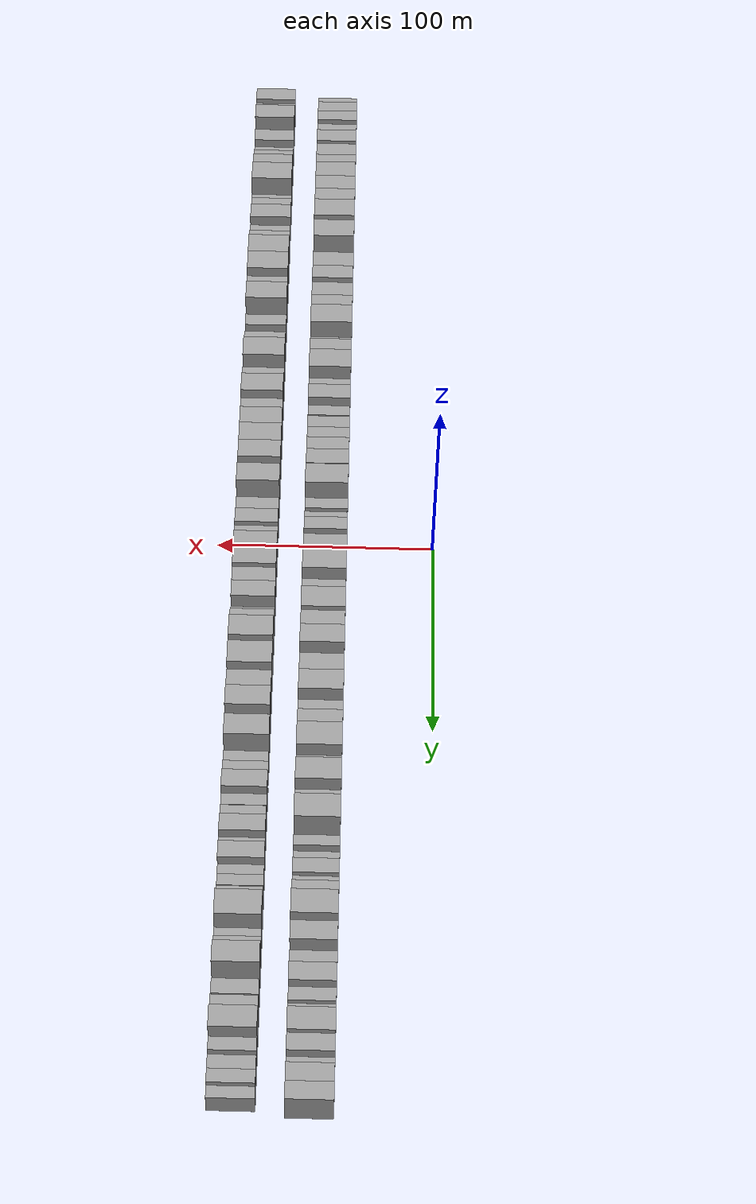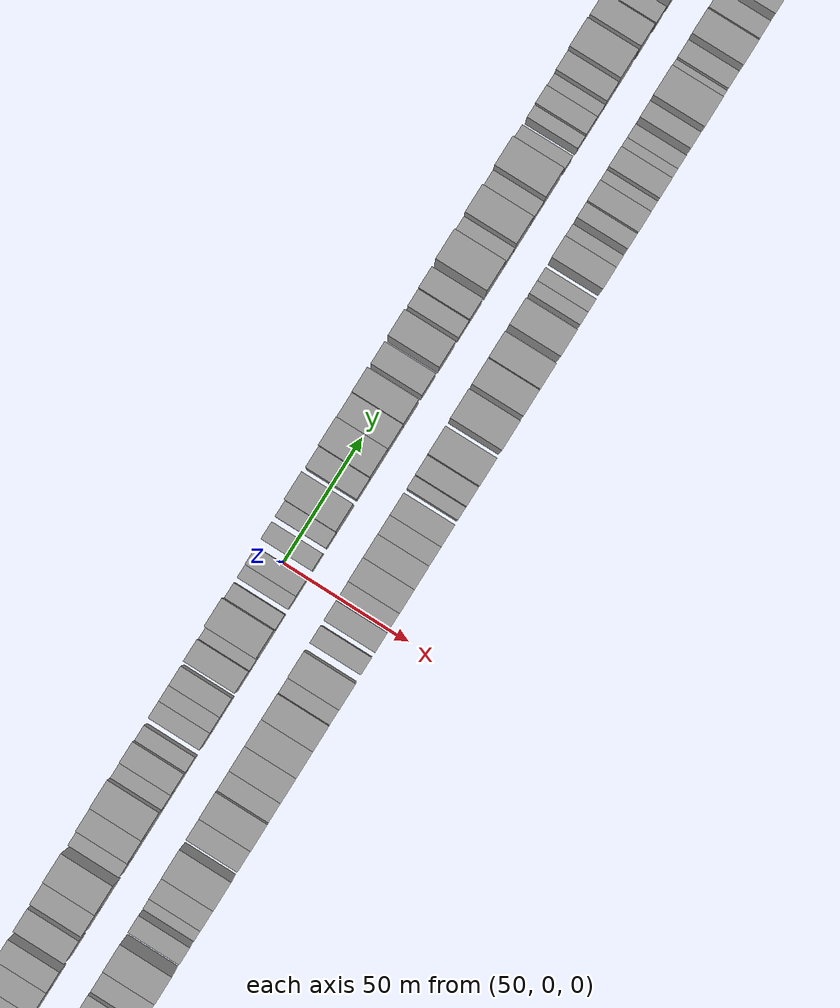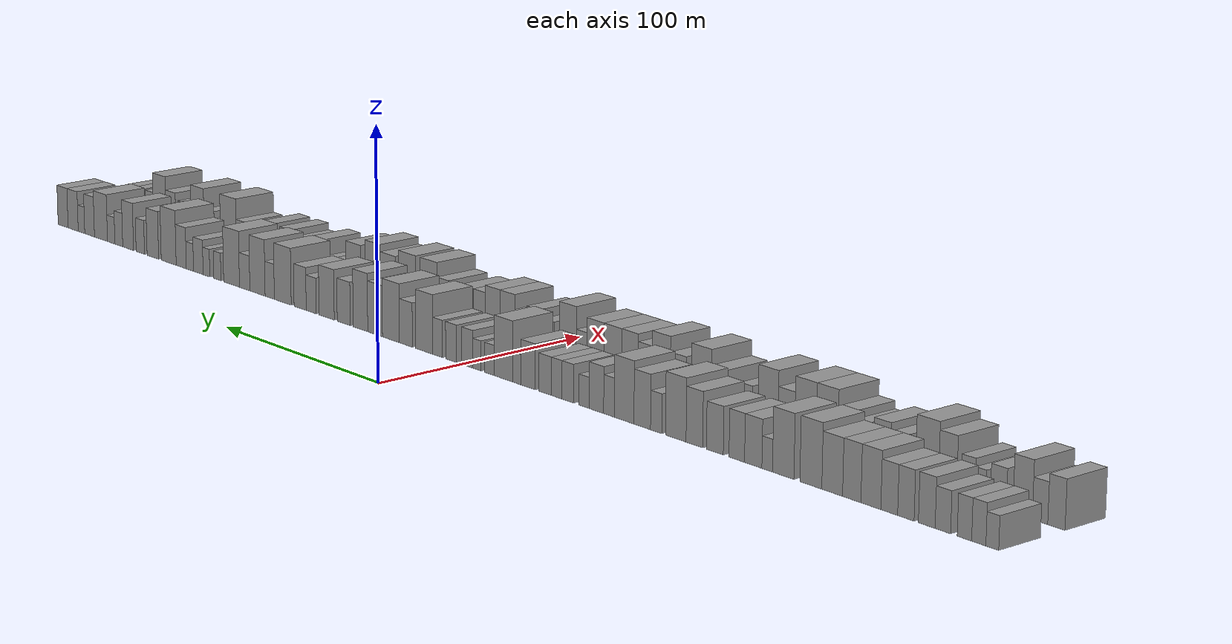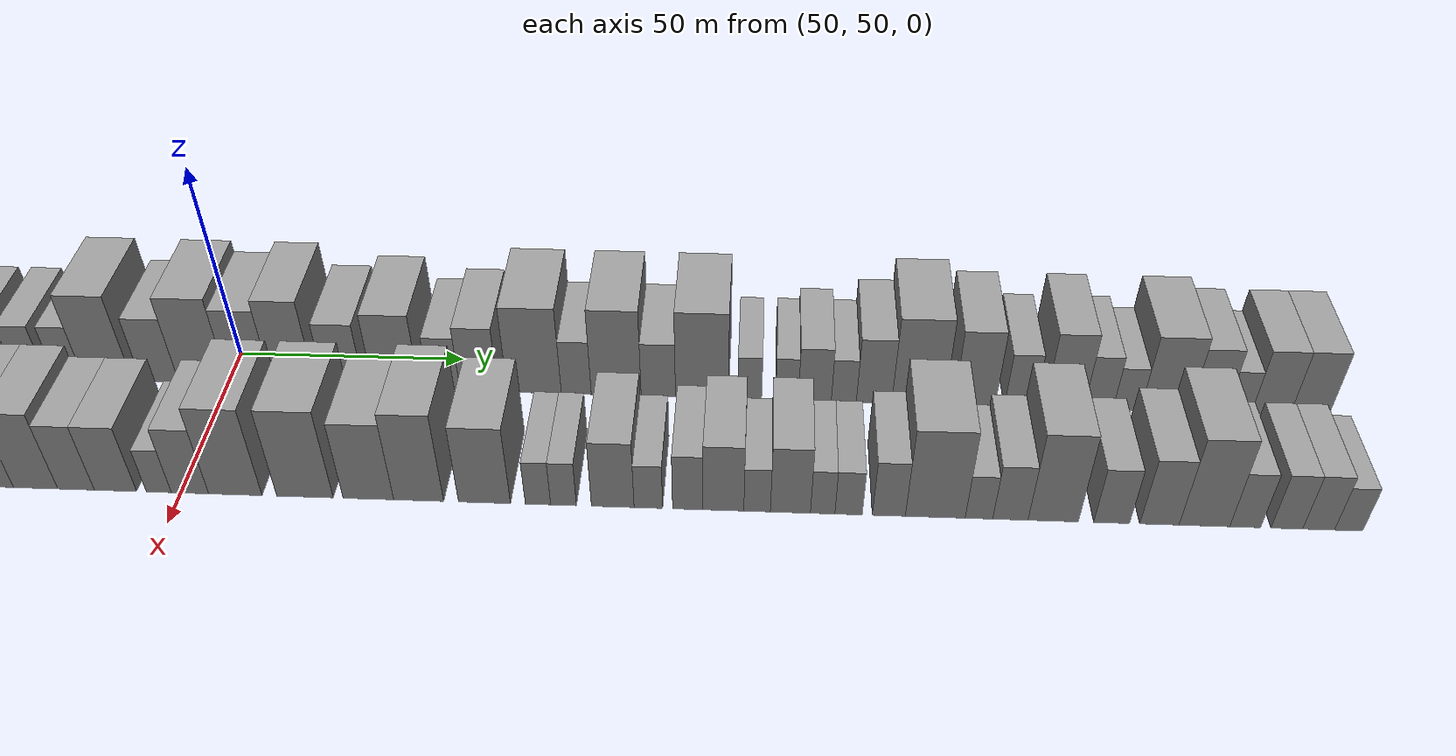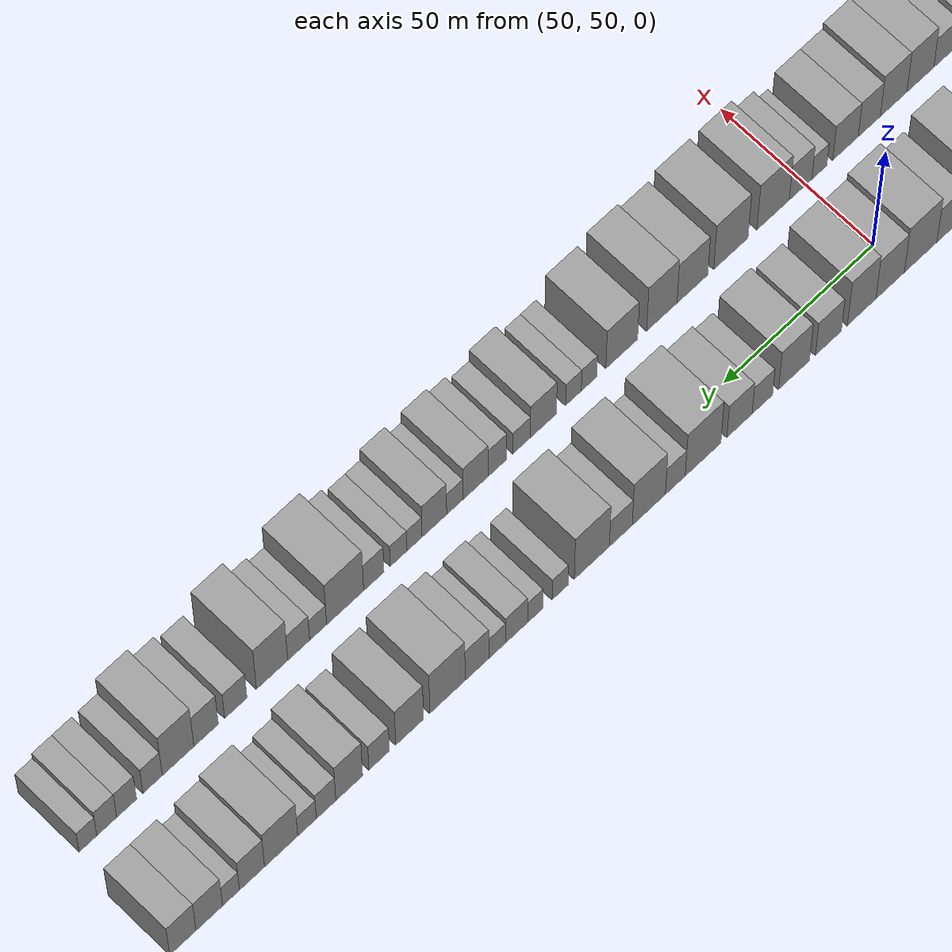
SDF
<sdf version="1.6">
 <world name="default">
  <scene>
   <sky><clouds><speed>12</speed></clouds></sky>
   <ambient>0.4 0.4 0.4 1</ambient>
   <background>0.7 0.7 0.7 1</background>
   <shadows>1</shadows>
  </scene>
  <gravity>0 0 -9.8066</gravity>
  <magnetic_field>6e-06 2.3e-05 -4.2e-05</magnetic_field>
  <physics default="0" name="default_physics" type="ode">
   <ode>
    <solver>
     <type>quick</type>
     <iters>10</iters>
     <sor>1.0</sor>
     <use_dynamic_moi_rescaling>0</use_dynamic_moi_rescaling>
    </solver>
    <constraints>
     <cfm>0</cfm>
     <erp>0.2</erp>
     <contact_max_correcting_vel>100</contact_max_correcting_vel>
     <contact_surface_layer>0.001</contact_surface_layer>
    </constraints>
   </ode>
   <max_step_size>0.004</max_step_size>
   <real_time_factor>1</real_time_factor>
   <real_time_update_rate>250</real_time_update_rate>
  </physics>
  <light name="sun" type="directional">
   <pose>0 0 10 0 0 0</pose>
   <diffuse>0.8 0.8 0.8 1</diffuse>
   <specular>0.2 0.2 0.2 1</specular>
   <attenuation>
    <range>1000</range>
    <constant>0.9</constant>
    <linear>0.01</linear>
    <quadratic>0.001</quadratic>
   </attenuation>
   <direction>-0.5 0.1 -0.9</direction>
  </light>
  <model name="building_1">
   <static>1</static>
   <pose>50.0000 -279.1271 0 0.000000 0.000000 0.000000</pose>
   <link name="link">
    <pose>0 0 6.00 0 0 0</pose>
    <collision name="collision"><geometry><box><size>20.0000 5.7459 12.0000</size></box></geometry></collision>
    <visual name="visual">
     <cast_shadows>0</cast_shadows>
     <geometry><box><size>20.0000 5.7459 12.0000</size></box></geometry>
     <material>
      <script>
       <uri>model://grey_wall/materials/scripts</uri>
       <uri>model://grey_wall/materials/textures</uri>
       <name>vrc/grey_wall</name>
      </script>
     </material>
    </visual>
   </link>
  </model>
  <model name="building_2">
   <static>1</static>
   <pose>50.0000 -273.0447 0 0.000000 0.000000 0.000000</pose>
   <link name="link">
    <pose>0 0 7.50 0 0 0</pose>
    <collision name="collision"><geometry><box><size>20.0000 6.4189 15.0000</size></box></geometry></collision>
    <visual name="visual">
     <cast_shadows>0</cast_shadows>
     <geometry><box><size>20.0000 6.4189 15.0000</size></box></geometry>
     <material>
      <script>
       <uri>model://grey_wall/materials/scripts</uri>
       <uri>model://grey_wall/materials/textures</uri>
       <name>vrc/grey_wall</name>
      </script>
     </material>
    </visual>
   </link>
  </model>
  <model name="building_3">
   <static>1</static>
   <pose>50.0000 -266.5574 0 0.000000 0.000000 0.000000</pose>
   <link name="link">
    <pose>0 0 7.50 0 0 0</pose>
    <collision name="collision"><geometry><box><size>20.0000 6.5558 15.0000</size></box></geometry></collision>
    <visual name="visual">
     <cast_shadows>0</cast_shadows>
     <geometry><box><size>20.0000 6.5558 15.0000</size></box></geometry>
     <material>
      <script>
       <uri>model://grey_wall/materials/scripts</uri>
       <uri>model://grey_wall/materials/textures</uri>
       <name>vrc/grey_wall</name>
      </script>
     </material>
    </visual>
   </link>
  </model>
  <model name="building_4">
   <static>1</static>
   <pose>50.0000 -256.7154 0 0.000000 0.000000 0.000000</pose>
   <link name="link">
    <pose>0 0 7.50 0 0 0</pose>
    <collision name="collision"><geometry><box><size>20.0000 7.1282 15.0000</size></box></geometry></collision>
    <visual name="visual">
     <cast_shadows>0</cast_shadows>
     <geometry><box><size>20.0000 7.1282 15.0000</size></box></geometry>
     <material>
      <script>
       <uri>model://grey_wall/materials/scripts</uri>
       <uri>model://grey_wall/materials/textures</uri>
       <name>vrc/grey_wall</name>
      </script>
     </material>
    </visual>
   </link>
  </model>
  <model name="building_5">
   <static>1</static>
   <pose>50.0000 -249.2632 0 0.000000 0.000000 0.000000</pose>
   <link name="link">
    <pose>0 0 9.00 0 0 0</pose>
    <collision name="collision"><geometry><box><size>20.0000 7.7762 18.0000</size></box></geometry></collision>
    <visual name="visual">
     <cast_shadows>0</cast_shadows>
     <geometry><box><size>20.0000 7.7762 18.0000</size></box></geometry>
     <material>
      <script>
       <uri>model://grey_wall/materials/scripts</uri>
       <uri>model://grey_wall/materials/textures</uri>
       <name>vrc/grey_wall</name>
      </script>
     </material>
    </visual>
   </link>
  </model>
  <model name="building_6">
   <static>1</static>
   <pose>50.0000 -239.5126 0 0.000000 0.000000 0.000000</pose>
   <link name="link">
    <pose>0 0 9.00 0 0 0</pose>
    <collision name="collision"><geometry><box><size>20.0000 7.7250 18.0000</size></box></geometry></collision>
    <visual name="visual">
     <cast_shadows>0</cast_shadows>
     <geometry><box><size>20.0000 7.7250 18.0000</size></box></geometry>
     <material>
      <script>
       <uri>model://grey_wall/materials/scripts</uri>
       <uri>model://grey_wall/materials/textures</uri>
       <name>vrc/grey_wall</name>
      </script>
     </material>
    </visual>
   </link>
  </model>
  <model name="building_7">
   <static>1</static>
   <pose>50.0000 -231.6655 0 0.000000 0.000000 0.000000</pose>
   <link name="link">
    <pose>0 0 9.00 0 0 0</pose>
    <collision name="collision"><geometry><box><size>20.0000 7.9691 18.0000</size></box></geometry></collision>
    <visual name="visual">
     <cast_shadows>0</cast_shadows>
     <geometry><box><size>20.0000 7.9691 18.0000</size></box></geometry>
     <material>
      <script>
       <uri>model://grey_wall/materials/scripts</uri>
       <uri>model://grey_wall/materials/textures</uri>
       <name>vrc/grey_wall</name>
      </script>
     </material>
    </visual>
   </link>
  </model>
  <model name="building_8">
   <static>1</static>
   <pose>50.0000 -222.8988 0 0.000000 0.000000 0.000000</pose>
   <link name="link">
    <pose>0 0 10.50 0 0 0</pose>
    <collision name="collision"><geometry><box><size>20.0000 9.5644 21.0000</size></box></geometry></collision>
    <visual name="visual">
     <cast_shadows>0</cast_shadows>
     <geometry><box><size>20.0000 9.5644 21.0000</size></box></geometry>
     <material>
      <script>
       <uri>model://grey_wall/materials/scripts</uri>
       <uri>model://grey_wall/materials/textures</uri>
       <name>vrc/grey_wall</name>
      </script>
     </material>
    </visual>
   </link>
  </model>
  <model name="building_9">
   <static>1</static>
   <pose>50.0000 -213.6746 0 0.000000 0.000000 0.000000</pose>
   <link name="link">
    <pose>0 0 10.50 0 0 0</pose>
    <collision name="collision"><geometry><box><size>20.0000 8.8841 21.0000</size></box></geometry></collision>
    <visual name="visual">
     <cast_shadows>0</cast_shadows>
     <geometry><box><size>20.0000 8.8841 21.0000</size></box></geometry>
     <material>
      <script>
       <uri>model://grey_wall/materials/scripts</uri>
       <uri>model://grey_wall/materials/textures</uri>
       <name>vrc/grey_wall</name>
      </script>
     </material>
    </visual>
   </link>
  </model>
  <model name="building_10">
   <static>1</static>
   <pose>50.0000 -204.1396 0 0.000000 0.000000 0.000000</pose>
   <link name="link">
    <pose>0 0 10.50 0 0 0</pose>
    <collision name="collision"><geometry><box><size>20.0000 10.1860 21.0000</size></box></geometry></collision>
    <visual name="visual">
     <cast_shadows>0</cast_shadows>
     <geometry><box><size>20.0000 10.1860 21.0000</size></box></geometry>
     <material>
      <script>
       <uri>model://grey_wall/materials/scripts</uri>
       <uri>model://grey_wall/materials/textures</uri>
       <name>vrc/grey_wall</name>
      </script>
     </material>
    </visual>
   </link>
  </model>
  <model name="building_11">
   <static>1</static>
   <pose>50.0000 -193.5970 0 0.000000 0.000000 0.000000</pose>
   <link name="link">
    <pose>0 0 12.00 0 0 0</pose>
    <collision name="collision"><geometry><box><size>20.0000 10.8992 24.0000</size></box></geometry></collision>
    <visual name="visual">
     <cast_shadows>0</cast_shadows>
     <geometry><box><size>20.0000 10.8992 24.0000</size></box></geometry>
     <material>
      <script>
       <uri>model://grey_wall/materials/scripts</uri>
       <uri>model://grey_wall/materials/textures</uri>
       <name>vrc/grey_wall</name>
      </script>
     </material>
    </visual>
   </link>
  </model>
  <model name="building_12">
   <static>1</static>
   <pose>50.0000 -179.7389 0 0.000000 0.000000 0.000000</pose>
   <link name="link">
    <pose>0 0 12.00 0 0 0</pose>
    <collision name="collision"><geometry><box><size>20.0000 10.8170 24.0000</size></box></geometry></collision>
    <visual name="visual">
     <cast_shadows>0</cast_shadows>
     <geometry><box><size>20.0000 10.8170 24.0000</size></box></geometry>
     <material>
      <script>
       <uri>model://grey_wall/materials/scripts</uri>
       <uri>model://grey_wall/materials/textures</uri>
       <name>vrc/grey_wall</name>
      </script>
     </material>
    </visual>
   </link>
  </model>
  <model name="building_13">
   <static>1</static>
   <pose>50.0000 -171.6334 0 0.000000 0.000000 0.000000</pose>
   <link name="link">
    <pose>0 0 6.00 0 0 0</pose>
    <collision name="collision"><geometry><box><size>20.0000 5.3941 12.0000</size></box></geometry></collision>
    <visual name="visual">
     <cast_shadows>0</cast_shadows>
     <geometry><box><size>20.0000 5.3941 12.0000</size></box></geometry>
     <material>
      <script>
       <uri>model://grey_wall/materials/scripts</uri>
       <uri>model://grey_wall/materials/textures</uri>
       <name>vrc/grey_wall</name>
      </script>
     </material>
    </visual>
   </link>
  </model>
  <model name="building_14">
   <static>1</static>
   <pose>50.0000 -164.4834 0 0.000000 0.000000 0.000000</pose>
   <link name="link">
    <pose>0 0 9.00 0 0 0</pose>
    <collision name="collision"><geometry><box><size>20.0000 8.9060 18.0000</size></box></geometry></collision>
    <visual name="visual">
     <cast_shadows>0</cast_shadows>
     <geometry><box><size>20.0000 8.9060 18.0000</size></box></geometry>
     <material>
      <script>
       <uri>model://grey_wall/materials/scripts</uri>
       <uri>model://grey_wall/materials/textures</uri>
       <name>vrc/grey_wall</name>
      </script>
     </material>
    </visual>
   </link>
  </model>
  <model name="building_15">
   <static>1</static>
   <pose>50.0000 -155.9993 0 0.000000 0.000000 0.000000</pose>
   <link name="link">
    <pose>0 0 9.00 0 0 0</pose>
    <collision name="collision"><geometry><box><size>20.0000 8.0620 18.0000</size></box></geometry></collision>
    <visual name="visual">
     <cast_shadows>0</cast_shadows>
     <geometry><box><size>20.0000 8.0620 18.0000</size></box></geometry>
     <material>
      <script>
       <uri>model://grey_wall/materials/scripts</uri>
       <uri>model://grey_wall/materials/textures</uri>
       <name>vrc/grey_wall</name>
      </script>
     </material>
    </visual>
   </link>
  </model>
  <model name="building_16">
   <static>1</static>
   <pose>50.0000 -144.5254 0 0.000000 0.000000 0.000000</pose>
   <link name="link">
    <pose>0 0 9.00 0 0 0</pose>
    <collision name="collision"><geometry><box><size>20.0000 8.8857 18.0000</size></box></geometry></collision>
    <visual name="visual">
     <cast_shadows>0</cast_shadows>
     <geometry><box><size>20.0000 8.8857 18.0000</size></box></geometry>
     <material>
      <script>
       <uri>model://grey_wall/materials/scripts</uri>
       <uri>model://grey_wall/materials/textures</uri>
       <name>vrc/grey_wall</name>
      </script>
     </material>
    </visual>
   </link>
  </model>
  <model name="building_17">
   <static>1</static>
   <pose>50.0000 -133.6724 0 0.000000 0.000000 0.000000</pose>
   <link name="link">
    <pose>0 0 10.50 0 0 0</pose>
    <collision name="collision"><geometry><box><size>20.0000 8.8204 21.0000</size></box></geometry></collision>
    <visual name="visual">
     <cast_shadows>0</cast_shadows>
     <geometry><box><size>20.0000 8.8204 21.0000</size></box></geometry>
     <material>
      <script>
       <uri>model://grey_wall/materials/scripts</uri>
       <uri>model://grey_wall/materials/textures</uri>
       <name>vrc/grey_wall</name>
      </script>
     </material>
    </visual>
   </link>
  </model>
  <model name="building_18">
   <static>1</static>
   <pose>50.0000 -123.7028 0 0.000000 0.000000 0.000000</pose>
   <link name="link">
    <pose>0 0 12.00 0 0 0</pose>
    <collision name="collision"><geometry><box><size>20.0000 11.1187 24.0000</size></box></geometry></collision>
    <visual name="visual">
     <cast_shadows>0</cast_shadows>
     <geometry><box><size>20.0000 11.1187 24.0000</size></box></geometry>
     <material>
      <script>
       <uri>model://grey_wall/materials/scripts</uri>
       <uri>model://grey_wall/materials/textures</uri>
       <name>vrc/grey_wall</name>
      </script>
     </material>
    </visual>
   </link>
  </model>
  <model name="building_19">
   <static>1</static>
   <pose>50.0000 -113.0769 0 0.000000 0.000000 0.000000</pose>
   <link name="link">
    <pose>0 0 7.50 0 0 0</pose>
    <collision name="collision"><geometry><box><size>20.0000 6.1330 15.0000</size></box></geometry></collision>
    <visual name="visual">
     <cast_shadows>0</cast_shadows>
     <geometry><box><size>20.0000 6.1330 15.0000</size></box></geometry>
     <material>
      <script>
       <uri>model://grey_wall/materials/scripts</uri>
       <uri>model://grey_wall/materials/textures</uri>
       <name>vrc/grey_wall</name>
      </script>
     </material>
    </visual>
   </link>
  </model>
  <model name="building_20">
   <static>1</static>
   <pose>50.0000 -105.4436 0 0.000000 0.000000 0.000000</pose>
   <link name="link">
    <pose>0 0 10.50 0 0 0</pose>
    <collision name="collision"><geometry><box><size>20.0000 9.1338 21.0000</size></box></geometry></collision>
    <visual name="visual">
     <cast_shadows>0</cast_shadows>
     <geometry><box><size>20.0000 9.1338 21.0000</size></box></geometry>
     <material>
      <script>
       <uri>model://grey_wall/materials/scripts</uri>
       <uri>model://grey_wall/materials/textures</uri>
       <name>vrc/grey_wall</name>
      </script>
     </material>
    </visual>
   </link>
  </model>
  <model name="building_21">
   <static>1</static>
   <pose>50.0000 -95.4409 0 0.000000 0.000000 0.000000</pose>
   <link name="link">
    <pose>0 0 12.00 0 0 0</pose>
    <collision name="collision"><geometry><box><size>20.0000 10.8715 24.0000</size></box></geometry></collision>
    <visual name="visual">
     <cast_shadows>0</cast_shadows>
     <geometry><box><size>20.0000 10.8715 24.0000</size></box></geometry>
     <material>
      <script>
       <uri>model://grey_wall/materials/scripts</uri>
       <uri>model://grey_wall/materials/textures</uri>
       <name>vrc/grey_wall</name>
      </script>
     </material>
    </visual>
   </link>
  </model>
  <model name="building_22">
   <static>1</static>
   <pose>50.0000 -86.9923 0 0.000000 0.000000 0.000000</pose>
   <link name="link">
    <pose>0 0 7.50 0 0 0</pose>
    <collision name="collision"><geometry><box><size>20.0000 6.0256 15.0000</size></box></geometry></collision>
    <visual name="visual">
     <cast_shadows>0</cast_shadows>
     <geometry><box><size>20.0000 6.0256 15.0000</size></box></geometry>
     <material>
      <script>
       <uri>model://grey_wall/materials/scripts</uri>
       <uri>model://grey_wall/materials/textures</uri>
       <name>vrc/grey_wall</name>
      </script>
     </material>
    </visual>
   </link>
  </model>
  <model name="building_23">
   <static>1</static>
   <pose>50.0000 -79.8421 0 0.000000 0.000000 0.000000</pose>
   <link name="link">
    <pose>0 0 9.00 0 0 0</pose>
    <collision name="collision"><geometry><box><size>20.0000 8.2749 18.0000</size></box></geometry></collision>
    <visual name="visual">
     <cast_shadows>0</cast_shadows>
     <geometry><box><size>20.0000 8.2749 18.0000</size></box></geometry>
     <material>
      <script>
       <uri>model://grey_wall/materials/scripts</uri>
       <uri>model://grey_wall/materials/textures</uri>
       <name>vrc/grey_wall</name>
      </script>
     </material>
    </visual>
   </link>
  </model>
  <model name="building_24">
   <static>1</static>
   <pose>50.0000 -72.7355 0 0.000000 0.000000 0.000000</pose>
   <link name="link">
    <pose>0 0 6.00 0 0 0</pose>
    <collision name="collision"><geometry><box><size>20.0000 5.9383 12.0000</size></box></geometry></collision>
    <visual name="visual">
     <cast_shadows>0</cast_shadows>
     <geometry><box><size>20.0000 5.9383 12.0000</size></box></geometry>
     <material>
      <script>
       <uri>model://grey_wall/materials/scripts</uri>
       <uri>model://grey_wall/materials/textures</uri>
       <name>vrc/grey_wall</name>
      </script>
     </material>
    </visual>
   </link>
  </model>
  <model name="building_25">
   <static>1</static>
   <pose>50.0000 -63.4808 0 0.000000 0.000000 0.000000</pose>
   <link name="link">
    <pose>0 0 7.50 0 0 0</pose>
    <collision name="collision"><geometry><box><size>20.0000 6.5712 15.0000</size></box></geometry></collision>
    <visual name="visual">
     <cast_shadows>0</cast_shadows>
     <geometry><box><size>20.0000 6.5712 15.0000</size></box></geometry>
     <material>
      <script>
       <uri>model://grey_wall/materials/scripts</uri>
       <uri>model://grey_wall/materials/textures</uri>
       <name>vrc/grey_wall</name>
      </script>
     </material>
    </visual>
   </link>
  </model>
  <model name="building_26">
   <static>1</static>
   <pose>50.0000 -57.1335 0 0.000000 0.000000 0.000000</pose>
   <link name="link">
    <pose>0 0 7.50 0 0 0</pose>
    <collision name="collision"><geometry><box><size>20.0000 6.1234 15.0000</size></box></geometry></collision>
    <visual name="visual">
     <cast_shadows>0</cast_shadows>
     <geometry><box><size>20.0000 6.1234 15.0000</size></box></geometry>
     <material>
      <script>
       <uri>model://grey_wall/materials/scripts</uri>
       <uri>model://grey_wall/materials/textures</uri>
       <name>vrc/grey_wall</name>
      </script>
     </material>
    </visual>
   </link>
  </model>
  <model name="building_27">
   <static>1</static>
   <pose>50.0000 -50.3300 0 0.000000 0.000000 0.000000</pose>
   <link name="link">
    <pose>0 0 7.50 0 0 0</pose>
    <collision name="collision"><geometry><box><size>20.0000 7.4836 15.0000</size></box></geometry></collision>
    <visual name="visual">
     <cast_shadows>0</cast_shadows>
     <geometry><box><size>20.0000 7.4836 15.0000</size></box></geometry>
     <material>
      <script>
       <uri>model://grey_wall/materials/scripts</uri>
       <uri>model://grey_wall/materials/textures</uri>
       <name>vrc/grey_wall</name>
      </script>
     </material>
    </visual>
   </link>
  </model>
  <model name="building_28">
   <static>1</static>
   <pose>50.0000 -40.3226 0 0.000000 0.000000 0.000000</pose>
   <link name="link">
    <pose>0 0 9.00 0 0 0</pose>
    <collision name="collision"><geometry><box><size>20.0000 8.5311 18.0000</size></box></geometry></collision>
    <visual name="visual">
     <cast_shadows>0</cast_shadows>
     <geometry><box><size>20.0000 8.5311 18.0000</size></box></geometry>
     <material>
      <script>
       <uri>model://grey_wall/materials/scripts</uri>
       <uri>model://grey_wall/materials/textures</uri>
       <name>vrc/grey_wall</name>
      </script>
     </material>
    </visual>
   </link>
  </model>
  <model name="building_29">
   <static>1</static>
   <pose>50.0000 -33.5444 0 0.000000 0.000000 0.000000</pose>
   <link name="link">
    <pose>0 0 6.00 0 0 0</pose>
    <collision name="collision"><geometry><box><size>20.0000 5.0253 12.0000</size></box></geometry></collision>
    <visual name="visual">
     <cast_shadows>0</cast_shadows>
     <geometry><box><size>20.0000 5.0253 12.0000</size></box></geometry>
     <material>
      <script>
       <uri>model://grey_wall/materials/scripts</uri>
       <uri>model://grey_wall/materials/textures</uri>
       <name>vrc/grey_wall</name>
      </script>
     </material>
    </visual>
   </link>
  </model>
  <model name="building_30">
   <static>1</static>
   <pose>50.0000 -25.5399 0 0.000000 0.000000 0.000000</pose>
   <link name="link">
    <pose>0 0 12.00 0 0 0</pose>
    <collision name="collision"><geometry><box><size>20.0000 10.9839 24.0000</size></box></geometry></collision>
    <visual name="visual">
     <cast_shadows>0</cast_shadows>
     <geometry><box><size>20.0000 10.9839 24.0000</size></box></geometry>
     <material>
      <script>
       <uri>model://grey_wall/materials/scripts</uri>
       <uri>model://grey_wall/materials/textures</uri>
       <name>vrc/grey_wall</name>
      </script>
     </material>
    </visual>
   </link>
  </model>
  <model name="building_31">
   <static>1</static>
   <pose>50.0000 -17.0664 0 0.000000 0.000000 0.000000</pose>
   <link name="link">
    <pose>0 0 6.00 0 0 0</pose>
    <collision name="collision"><geometry><box><size>20.0000 5.9630 12.0000</size></box></geometry></collision>
    <visual name="visual">
     <cast_shadows>0</cast_shadows>
     <geometry><box><size>20.0000 5.9630 12.0000</size></box></geometry>
     <material>
      <script>
       <uri>model://grey_wall/materials/scripts</uri>
       <uri>model://grey_wall/materials/textures</uri>
       <name>vrc/grey_wall</name>
      </script>
     </material>
    </visual>
   </link>
  </model>
  <model name="building_32">
   <static>1</static>
   <pose>50.0000 -9.5137 0 0.000000 0.000000 0.000000</pose>
   <link name="link">
    <pose>0 0 6.00 0 0 0</pose>
    <collision name="collision"><geometry><box><size>20.0000 5.1426 12.0000</size></box></geometry></collision>
    <visual name="visual">
     <cast_shadows>0</cast_shadows>
     <geometry><box><size>20.0000 5.1426 12.0000</size></box></geometry>
     <material>
      <script>
       <uri>model://grey_wall/materials/scripts</uri>
       <uri>model://grey_wall/materials/textures</uri>
       <name>vrc/grey_wall</name>
      </script>
     </material>
    </visual>
   </link>
  </model>
  <model name="building_33">
   <static>1</static>
   <pose>50.0000 -3.4888 0 0.000000 0.000000 0.000000</pose>
   <link name="link">
    <pose>0 0 7.50 0 0 0</pose>
    <collision name="collision"><geometry><box><size>20.0000 6.9071 15.0000</size></box></geometry></collision>
    <visual name="visual">
     <cast_shadows>0</cast_shadows>
     <geometry><box><size>20.0000 6.9071 15.0000</size></box></geometry>
     <material>
      <script>
       <uri>model://grey_wall/materials/scripts</uri>
       <uri>model://grey_wall/materials/textures</uri>
       <name>vrc/grey_wall</name>
      </script>
     </material>
    </visual>
   </link>
  </model>
  <model name="building_34">
   <static>1</static>
   <pose>50.0000 6.3638 0 0.000000 0.000000 0.000000</pose>
   <link name="link">
    <pose>0 0 7.50 0 0 0</pose>
    <collision name="collision"><geometry><box><size>20.0000 6.7982 15.0000</size></box></geometry></collision>
    <visual name="visual">
     <cast_shadows>0</cast_shadows>
     <geometry><box><size>20.0000 6.7982 15.0000</size></box></geometry>
     <material>
      <script>
       <uri>model://grey_wall/materials/scripts</uri>
       <uri>model://grey_wall/materials/textures</uri>
       <name>vrc/grey_wall</name>
      </script>
     </material>
    </visual>
   </link>
  </model>
  <model name="building_35">
   <static>1</static>
   <pose>50.0000 14.8870 0 0.000000 0.000000 0.000000</pose>
   <link name="link">
    <pose>0 0 7.50 0 0 0</pose>
    <collision name="collision"><geometry><box><size>20.0000 6.2482 15.0000</size></box></geometry></collision>
    <visual name="visual">
     <cast_shadows>0</cast_shadows>
     <geometry><box><size>20.0000 6.2482 15.0000</size></box></geometry>
     <material>
      <script>
       <uri>model://grey_wall/materials/scripts</uri>
       <uri>model://grey_wall/materials/textures</uri>
       <name>vrc/grey_wall</name>
      </script>
     </material>
    </visual>
   </link>
  </model>
  <model name="building_36">
   <static>1</static>
   <pose>50.0000 23.4039 0 0.000000 0.000000 0.000000</pose>
   <link name="link">
    <pose>0 0 12.00 0 0 0</pose>
    <collision name="collision"><geometry><box><size>20.0000 10.7855 24.0000</size></box></geometry></collision>
    <visual name="visual">
     <cast_shadows>0</cast_shadows>
     <geometry><box><size>20.0000 10.7855 24.0000</size></box></geometry>
     <material>
      <script>
       <uri>model://grey_wall/materials/scripts</uri>
       <uri>model://grey_wall/materials/textures</uri>
       <name>vrc/grey_wall</name>
      </script>
     </material>
    </visual>
   </link>
  </model>
  <model name="building_37">
   <static>1</static>
   <pose>50.0000 34.9487 0 0.000000 0.000000 0.000000</pose>
   <link name="link">
    <pose>0 0 9.00 0 0 0</pose>
    <collision name="collision"><geometry><box><size>20.0000 8.3042 18.0000</size></box></geometry></collision>
    <visual name="visual">
     <cast_shadows>0</cast_shadows>
     <geometry><box><size>20.0000 8.3042 18.0000</size></box></geometry>
     <material>
      <script>
       <uri>model://grey_wall/materials/scripts</uri>
       <uri>model://grey_wall/materials/textures</uri>
       <name>vrc/grey_wall</name>
      </script>
     </material>
    </visual>
   </link>
  </model>
  <model name="building_38">
   <static>1</static>
   <pose>50.0000 44.6083 0 0.000000 0.000000 0.000000</pose>
   <link name="link">
    <pose>0 0 12.00 0 0 0</pose>
    <collision name="collision"><geometry><box><size>20.0000 11.0150 24.0000</size></box></geometry></collision>
    <visual name="visual">
     <cast_shadows>0</cast_shadows>
     <geometry><box><size>20.0000 11.0150 24.0000</size></box></geometry>
     <material>
      <script>
       <uri>model://grey_wall/materials/scripts</uri>
       <uri>model://grey_wall/materials/textures</uri>
       <name>vrc/grey_wall</name>
      </script>
     </material>
    </visual>
   </link>
  </model>
  <model name="building_39">
   <static>1</static>
   <pose>50.0000 54.9373 0 0.000000 0.000000 0.000000</pose>
   <link name="link">
    <pose>0 0 10.50 0 0 0</pose>
    <collision name="collision"><geometry><box><size>20.0000 9.6429 21.0000</size></box></geometry></collision>
    <visual name="visual">
     <cast_shadows>0</cast_shadows>
     <geometry><box><size>20.0000 9.6429 21.0000</size></box></geometry>
     <material>
      <script>
       <uri>model://grey_wall/materials/scripts</uri>
       <uri>model://grey_wall/materials/textures</uri>
       <name>vrc/grey_wall</name>
      </script>
     </material>
    </visual>
   </link>
  </model>
  <model name="building_40">
   <static>1</static>
   <pose>50.0000 64.5607 0 0.000000 0.000000 0.000000</pose>
   <link name="link">
    <pose>0 0 12.00 0 0 0</pose>
    <collision name="collision"><geometry><box><size>20.0000 9.6038 24.0000</size></box></geometry></collision>
    <visual name="visual">
     <cast_shadows>0</cast_shadows>
     <geometry><box><size>20.0000 9.6038 24.0000</size></box></geometry>
     <material>
      <script>
       <uri>model://grey_wall/materials/scripts</uri>
       <uri>model://grey_wall/materials/textures</uri>
       <name>vrc/grey_wall</name>
      </script>
     </material>
    </visual>
   </link>
  </model>
  <model name="building_41">
   <static>1</static>
   <pose>50.0000 75.7096 0 0.000000 0.000000 0.000000</pose>
   <link name="link">
    <pose>0 0 9.00 0 0 0</pose>
    <collision name="collision"><geometry><box><size>20.0000 8.6940 18.0000</size></box></geometry></collision>
    <visual name="visual">
     <cast_shadows>0</cast_shadows>
     <geometry><box><size>20.0000 8.6940 18.0000</size></box></geometry>
     <material>
      <script>
       <uri>model://grey_wall/materials/scripts</uri>
       <uri>model://grey_wall/materials/textures</uri>
       <name>vrc/grey_wall</name>
      </script>
     </material>
    </visual>
   </link>
  </model>
  <model name="building_42">
   <static>1</static>
   <pose>50.0000 87.1924 0 0.000000 0.000000 0.000000</pose>
   <link name="link">
    <pose>0 0 10.50 0 0 0</pose>
    <collision name="collision"><geometry><box><size>20.0000 10.2716 21.0000</size></box></geometry></collision>
    <visual name="visual">
     <cast_shadows>0</cast_shadows>
     <geometry><box><size>20.0000 10.2716 21.0000</size></box></geometry>
     <material>
      <script>
       <uri>model://grey_wall/materials/scripts</uri>
       <uri>model://grey_wall/materials/textures</uri>
       <name>vrc/grey_wall</name>
      </script>
     </material>
    </visual>
   </link>
  </model>
  <model name="building_43">
   <static>1</static>
   <pose>50.0000 97.7403 0 0.000000 0.000000 0.000000</pose>
   <link name="link">
    <pose>0 0 7.50 0 0 0</pose>
    <collision name="collision"><geometry><box><size>20.0000 6.8241 15.0000</size></box></geometry></collision>
    <visual name="visual">
     <cast_shadows>0</cast_shadows>
     <geometry><box><size>20.0000 6.8241 15.0000</size></box></geometry>
     <material>
      <script>
       <uri>model://grey_wall/materials/scripts</uri>
       <uri>model://grey_wall/materials/textures</uri>
       <name>vrc/grey_wall</name>
      </script>
     </material>
    </visual>
   </link>
  </model>
  <model name="building_44">
   <static>1</static>
   <pose>50.0000 105.3268 0 0.000000 0.000000 0.000000</pose>
   <link name="link">
    <pose>0 0 9.00 0 0 0</pose>
    <collision name="collision"><geometry><box><size>20.0000 8.3489 18.0000</size></box></geometry></collision>
    <visual name="visual">
     <cast_shadows>0</cast_shadows>
     <geometry><box><size>20.0000 8.3489 18.0000</size></box></geometry>
     <material>
      <script>
       <uri>model://grey_wall/materials/scripts</uri>
       <uri>model://grey_wall/materials/textures</uri>
       <name>vrc/grey_wall</name>
      </script>
     </material>
    </visual>
   </link>
  </model>
  <model name="building_45">
   <static>1</static>
   <pose>50.0000 117.3871 0 0.000000 0.000000 0.000000</pose>
   <link name="link">
    <pose>0 0 12.00 0 0 0</pose>
    <collision name="collision"><geometry><box><size>20.0000 11.7717 24.0000</size></box></geometry></collision>
    <visual name="visual">
     <cast_shadows>0</cast_shadows>
     <geometry><box><size>20.0000 11.7717 24.0000</size></box></geometry>
     <material>
      <script>
       <uri>model://grey_wall/materials/scripts</uri>
       <uri>model://grey_wall/materials/textures</uri>
       <name>vrc/grey_wall</name>
      </script>
     </material>
    </visual>
   </link>
  </model>
  <model name="building_46">
   <static>1</static>
   <pose>50.0000 126.5301 0 0.000000 0.000000 0.000000</pose>
   <link name="link">
    <pose>0 0 7.50 0 0 0</pose>
    <collision name="collision"><geometry><box><size>20.0000 6.5144 15.0000</size></box></geometry></collision>
    <visual name="visual">
     <cast_shadows>0</cast_shadows>
     <geometry><box><size>20.0000 6.5144 15.0000</size></box></geometry>
     <material>
      <script>
       <uri>model://grey_wall/materials/scripts</uri>
       <uri>model://grey_wall/materials/textures</uri>
       <name>vrc/grey_wall</name>
      </script>
     </material>
    </visual>
   </link>
  </model>
  <model name="building_47">
   <static>1</static>
   <pose>50.0000 135.2163 0 0.000000 0.000000 0.000000</pose>
   <link name="link">
    <pose>0 0 12.00 0 0 0</pose>
    <collision name="collision"><geometry><box><size>20.0000 10.8580 24.0000</size></box></geometry></collision>
    <visual name="visual">
     <cast_shadows>0</cast_shadows>
     <geometry><box><size>20.0000 10.8580 24.0000</size></box></geometry>
     <material>
      <script>
       <uri>model://grey_wall/materials/scripts</uri>
       <uri>model://grey_wall/materials/textures</uri>
       <name>vrc/grey_wall</name>
      </script>
     </material>
    </visual>
   </link>
  </model>
  <model name="building_48">
   <static>1</static>
   <pose>50.0000 144.3716 0 0.000000 0.000000 0.000000</pose>
   <link name="link">
    <pose>0 0 7.50 0 0 0</pose>
    <collision name="collision"><geometry><box><size>20.0000 7.4525 15.0000</size></box></geometry></collision>
    <visual name="visual">
     <cast_shadows>0</cast_shadows>
     <geometry><box><size>20.0000 7.4525 15.0000</size></box></geometry>
     <material>
      <script>
       <uri>model://grey_wall/materials/scripts</uri>
       <uri>model://grey_wall/materials/textures</uri>
       <name>vrc/grey_wall</name>
      </script>
     </material>
    </visual>
   </link>
  </model>
  <model name="building_49">
   <static>1</static>
   <pose>50.0000 153.8203 0 0.000000 0.000000 0.000000</pose>
   <link name="link">
    <pose>0 0 12.00 0 0 0</pose>
    <collision name="collision"><geometry><box><size>20.0000 11.4448 24.0000</size></box></geometry></collision>
    <visual name="visual">
     <cast_shadows>0</cast_shadows>
     <geometry><box><size>20.0000 11.4448 24.0000</size></box></geometry>
     <material>
      <script>
       <uri>model://grey_wall/materials/scripts</uri>
       <uri>model://grey_wall/materials/textures</uri>
       <name>vrc/grey_wall</name>
      </script>
     </material>
    </visual>
   </link>
  </model>
  <model name="building_50">
   <static>1</static>
   <pose>50.0000 164.1333 0 0.000000 0.000000 0.000000</pose>
   <link name="link">
    <pose>0 0 6.00 0 0 0</pose>
    <collision name="collision"><geometry><box><size>20.0000 5.1812 12.0000</size></box></geometry></collision>
    <visual name="visual">
     <cast_shadows>0</cast_shadows>
     <geometry><box><size>20.0000 5.1812 12.0000</size></box></geometry>
     <material>
      <script>
       <uri>model://grey_wall/materials/scripts</uri>
       <uri>model://grey_wall/materials/textures</uri>
       <name>vrc/grey_wall</name>
      </script>
     </material>
    </visual>
   </link>
  </model>
  <model name="building_51">
   <static>1</static>
   <pose>50.0000 172.1772 0 0.000000 0.000000 0.000000</pose>
   <link name="link">
    <pose>0 0 6.00 0 0 0</pose>
    <collision name="collision"><geometry><box><size>20.0000 4.9067 12.0000</size></box></geometry></collision>
    <visual name="visual">
     <cast_shadows>0</cast_shadows>
     <geometry><box><size>20.0000 4.9067 12.0000</size></box></geometry>
     <material>
      <script>
       <uri>model://grey_wall/materials/scripts</uri>
       <uri>model://grey_wall/materials/textures</uri>
       <name>vrc/grey_wall</name>
      </script>
     </material>
    </visual>
   </link>
  </model>
  <model name="building_52">
   <static>1</static>
   <pose>50.0000 178.1916 0 0.000000 0.000000 0.000000</pose>
   <link name="link">
    <pose>0 0 7.50 0 0 0</pose>
    <collision name="collision"><geometry><box><size>20.0000 7.1221 15.0000</size></box></geometry></collision>
    <visual name="visual">
     <cast_shadows>0</cast_shadows>
     <geometry><box><size>20.0000 7.1221 15.0000</size></box></geometry>
     <material>
      <script>
       <uri>model://grey_wall/materials/scripts</uri>
       <uri>model://grey_wall/materials/textures</uri>
       <name>vrc/grey_wall</name>
      </script>
     </material>
    </visual>
   </link>
  </model>
  <model name="building_53">
   <static>1</static>
   <pose>50.0000 184.4521 0 0.000000 0.000000 0.000000</pose>
   <link name="link">
    <pose>0 0 6.00 0 0 0</pose>
    <collision name="collision"><geometry><box><size>20.0000 5.3989 12.0000</size></box></geometry></collision>
    <visual name="visual">
     <cast_shadows>0</cast_shadows>
     <geometry><box><size>20.0000 5.3989 12.0000</size></box></geometry>
     <material>
      <script>
       <uri>model://grey_wall/materials/scripts</uri>
       <uri>model://grey_wall/materials/textures</uri>
       <name>vrc/grey_wall</name>
      </script>
     </material>
    </visual>
   </link>
  </model>
  <model name="building_54">
   <static>1</static>
   <pose>50.0000 190.9490 0 0.000000 0.000000 0.000000</pose>
   <link name="link">
    <pose>0 0 9.00 0 0 0</pose>
    <collision name="collision"><geometry><box><size>20.0000 7.5949 18.0000</size></box></geometry></collision>
    <visual name="visual">
     <cast_shadows>0</cast_shadows>
     <geometry><box><size>20.0000 7.5949 18.0000</size></box></geometry>
     <material>
      <script>
       <uri>model://grey_wall/materials/scripts</uri>
       <uri>model://grey_wall/materials/textures</uri>
       <name>vrc/grey_wall</name>
      </script>
     </material>
    </visual>
   </link>
  </model>
  <model name="building_55">
   <static>1</static>
   <pose>50.0000 200.3987 0 0.000000 0.000000 0.000000</pose>
   <link name="link">
    <pose>0 0 12.00 0 0 0</pose>
    <collision name="collision"><geometry><box><size>20.0000 11.3046 24.0000</size></box></geometry></collision>
    <visual name="visual">
     <cast_shadows>0</cast_shadows>
     <geometry><box><size>20.0000 11.3046 24.0000</size></box></geometry>
     <material>
      <script>
       <uri>model://grey_wall/materials/scripts</uri>
       <uri>model://grey_wall/materials/textures</uri>
       <name>vrc/grey_wall</name>
      </script>
     </material>
    </visual>
   </link>
  </model>
  <model name="building_56">
   <static>1</static>
   <pose>50.0000 212.4728 0 0.000000 0.000000 0.000000</pose>
   <link name="link">
    <pose>0 0 10.50 0 0 0</pose>
    <collision name="collision"><geometry><box><size>20.0000 8.8435 21.0000</size></box></geometry></collision>
    <visual name="visual">
     <cast_shadows>0</cast_shadows>
     <geometry><box><size>20.0000 8.8435 21.0000</size></box></geometry>
     <material>
      <script>
       <uri>model://grey_wall/materials/scripts</uri>
       <uri>model://grey_wall/materials/textures</uri>
       <name>vrc/grey_wall</name>
      </script>
     </material>
    </visual>
   </link>
  </model>
  <model name="building_57">
   <static>1</static>
   <pose>50.0000 222.1456 0 0.000000 0.000000 0.000000</pose>
   <link name="link">
    <pose>0 0 7.50 0 0 0</pose>
    <collision name="collision"><geometry><box><size>20.0000 6.5022 15.0000</size></box></geometry></collision>
    <visual name="visual">
     <cast_shadows>0</cast_shadows>
     <geometry><box><size>20.0000 6.5022 15.0000</size></box></geometry>
     <material>
      <script>
       <uri>model://grey_wall/materials/scripts</uri>
       <uri>model://grey_wall/materials/textures</uri>
       <name>vrc/grey_wall</name>
      </script>
     </material>
    </visual>
   </link>
  </model>
  <model name="building_58">
   <static>1</static>
   <pose>50.0000 231.6266 0 0.000000 0.000000 0.000000</pose>
   <link name="link">
    <pose>0 0 10.50 0 0 0</pose>
    <collision name="collision"><geometry><box><size>20.0000 8.4597 21.0000</size></box></geometry></collision>
    <visual name="visual">
     <cast_shadows>0</cast_shadows>
     <geometry><box><size>20.0000 8.4597 21.0000</size></box></geometry>
     <material>
      <script>
       <uri>model://grey_wall/materials/scripts</uri>
       <uri>model://grey_wall/materials/textures</uri>
       <name>vrc/grey_wall</name>
      </script>
     </material>
    </visual>
   </link>
  </model>
  <model name="building_59">
   <static>1</static>
   <pose>50.0000 238.9352 0 0.000000 0.000000 0.000000</pose>
   <link name="link">
    <pose>0 0 7.50 0 0 0</pose>
    <collision name="collision"><geometry><box><size>20.0000 6.1574 15.0000</size></box></geometry></collision>
    <visual name="visual">
     <cast_shadows>0</cast_shadows>
     <geometry><box><size>20.0000 6.1574 15.0000</size></box></geometry>
     <material>
      <script>
       <uri>model://grey_wall/materials/scripts</uri>
       <uri>model://grey_wall/materials/textures</uri>
       <name>vrc/grey_wall</name>
      </script>
     </material>
    </visual>
   </link>
  </model>
  <model name="building_60">
   <static>1</static>
   <pose>50.0000 244.9371 0 0.000000 0.000000 0.000000</pose>
   <link name="link">
    <pose>0 0 6.00 0 0 0</pose>
    <collision name="collision"><geometry><box><size>20.0000 5.8464 12.0000</size></box></geometry></collision>
    <visual name="visual">
     <cast_shadows>0</cast_shadows>
     <geometry><box><size>20.0000 5.8464 12.0000</size></box></geometry>
     <material>
      <script>
       <uri>model://grey_wall/materials/scripts</uri>
       <uri>model://grey_wall/materials/textures</uri>
       <name>vrc/grey_wall</name>
      </script>
     </material>
    </visual>
   </link>
  </model>
  <model name="building_61">
   <static>1</static>
   <pose>50.0000 253.0524 0 0.000000 0.000000 0.000000</pose>
   <link name="link">
    <pose>0 0 10.50 0 0 0</pose>
    <collision name="collision"><geometry><box><size>20.0000 10.3841 21.0000</size></box></geometry></collision>
    <visual name="visual">
     <cast_shadows>0</cast_shadows>
     <geometry><box><size>20.0000 10.3841 21.0000</size></box></geometry>
     <material>
      <script>
       <uri>model://grey_wall/materials/scripts</uri>
       <uri>model://grey_wall/materials/textures</uri>
       <name>vrc/grey_wall</name>
      </script>
     </material>
    </visual>
   </link>
  </model>
  <model name="building_62">
   <static>1</static>
   <pose>50.0000 262.1582 0 0.000000 0.000000 0.000000</pose>
   <link name="link">
    <pose>0 0 9.00 0 0 0</pose>
    <collision name="collision"><geometry><box><size>20.0000 7.8275 18.0000</size></box></geometry></collision>
    <visual name="visual">
     <cast_shadows>0</cast_shadows>
     <geometry><box><size>20.0000 7.8275 18.0000</size></box></geometry>
     <material>
      <script>
       <uri>model://grey_wall/materials/scripts</uri>
       <uri>model://grey_wall/materials/textures</uri>
       <name>vrc/grey_wall</name>
      </script>
     </material>
    </visual>
   </link>
  </model>
  <model name="building_63">
   <static>1</static>
   <pose>50.0000 268.7142 0 0.000000 0.000000 0.000000</pose>
   <link name="link">
    <pose>0 0 6.00 0 0 0</pose>
    <collision name="collision"><geometry><box><size>20.0000 5.2844 12.0000</size></box></geometry></collision>
    <visual name="visual">
     <cast_shadows>0</cast_shadows>
     <geometry><box><size>20.0000 5.2844 12.0000</size></box></geometry>
     <material>
      <script>
       <uri>model://grey_wall/materials/scripts</uri>
       <uri>model://grey_wall/materials/textures</uri>
       <name>vrc/grey_wall</name>
      </script>
     </material>
    </visual>
   </link>
  </model>
  <model name="building_64">
   <static>1</static>
   <pose>50.0000 275.4763 0 0.000000 0.000000 0.000000</pose>
   <link name="link">
    <pose>0 0 9.00 0 0 0</pose>
    <collision name="collision"><geometry><box><size>20.0000 8.2398 18.0000</size></box></geometry></collision>
    <visual name="visual">
     <cast_shadows>0</cast_shadows>
     <geometry><box><size>20.0000 8.2398 18.0000</size></box></geometry>
     <material>
      <script>
       <uri>model://grey_wall/materials/scripts</uri>
       <uri>model://grey_wall/materials/textures</uri>
       <name>vrc/grey_wall</name>
      </script>
     </material>
    </visual>
   </link>
  </model>
  <model name="building_65">
   <static>1</static>
   <pose>50.0000 283.6614 0 0.000000 0.000000 0.000000</pose>
   <link name="link">
    <pose>0 0 9.00 0 0 0</pose>
    <collision name="collision"><geometry><box><size>20.0000 8.1304 18.0000</size></box></geometry></collision>
    <visual name="visual">
     <cast_shadows>0</cast_shadows>
     <geometry><box><size>20.0000 8.1304 18.0000</size></box></geometry>
     <material>
      <script>
       <uri>model://grey_wall/materials/scripts</uri>
       <uri>model://grey_wall/materials/textures</uri>
       <name>vrc/grey_wall</name>
      </script>
     </material>
    </visual>
   </link>
  </model>
  <model name="building_66">
   <static>1</static>
   <pose>82.0000 -278.1258 0 0.000000 0.000000 0.000000</pose>
   <link name="link">
    <pose>0 0 9.00 0 0 0</pose>
    <collision name="collision"><geometry><box><size>20.0000 7.7484 18.0000</size></box></geometry></collision>
    <visual name="visual">
     <cast_shadows>0</cast_shadows>
     <geometry><box><size>20.0000 7.7484 18.0000</size></box></geometry>
     <material>
      <script>
       <uri>model://grey_wall/materials/scripts</uri>
       <uri>model://grey_wall/materials/textures</uri>
       <name>vrc/grey_wall</name>
      </script>
     </material>
    </visual>
   </link>
  </model>
  <model name="building_67">
   <static>1</static>
   <pose>82.0000 -270.7622 0 0.000000 0.000000 0.000000</pose>
   <link name="link">
    <pose>0 0 7.50 0 0 0</pose>
    <collision name="collision"><geometry><box><size>20.0000 6.9788 15.0000</size></box></geometry></collision>
    <visual name="visual">
     <cast_shadows>0</cast_shadows>
     <geometry><box><size>20.0000 6.9788 15.0000</size></box></geometry>
     <material>
      <script>
       <uri>model://grey_wall/materials/scripts</uri>
       <uri>model://grey_wall/materials/textures</uri>
       <name>vrc/grey_wall</name>
      </script>
     </material>
    </visual>
   </link>
  </model>
  <model name="building_68">
   <static>1</static>
   <pose>82.0000 -262.8454 0 0.000000 0.000000 0.000000</pose>
   <link name="link">
    <pose>0 0 10.50 0 0 0</pose>
    <collision name="collision"><geometry><box><size>20.0000 8.8550 21.0000</size></box></geometry></collision>
    <visual name="visual">
     <cast_shadows>0</cast_shadows>
     <geometry><box><size>20.0000 8.8550 21.0000</size></box></geometry>
     <material>
      <script>
       <uri>model://grey_wall/materials/scripts</uri>
       <uri>model://grey_wall/materials/textures</uri>
       <name>vrc/grey_wall</name>
      </script>
     </material>
    </visual>
   </link>
  </model>
  <model name="building_69">
   <static>1</static>
   <pose>82.0000 -251.6783 0 0.000000 0.000000 0.000000</pose>
   <link name="link">
    <pose>0 0 7.50 0 0 0</pose>
    <collision name="collision"><geometry><box><size>20.0000 7.4792 15.0000</size></box></geometry></collision>
    <visual name="visual">
     <cast_shadows>0</cast_shadows>
     <geometry><box><size>20.0000 7.4792 15.0000</size></box></geometry>
     <material>
      <script>
       <uri>model://grey_wall/materials/scripts</uri>
       <uri>model://grey_wall/materials/textures</uri>
       <name>vrc/grey_wall</name>
      </script>
     </material>
    </visual>
   </link>
  </model>
  <model name="building_70">
   <static>1</static>
   <pose>82.0000 -243.3795 0 0.000000 0.000000 0.000000</pose>
   <link name="link">
    <pose>0 0 6.00 0 0 0</pose>
    <collision name="collision"><geometry><box><size>20.0000 5.1184 12.0000</size></box></geometry></collision>
    <visual name="visual">
     <cast_shadows>0</cast_shadows>
     <geometry><box><size>20.0000 5.1184 12.0000</size></box></geometry>
     <material>
      <script>
       <uri>model://grey_wall/materials/scripts</uri>
       <uri>model://grey_wall/materials/textures</uri>
       <name>vrc/grey_wall</name>
      </script>
     </material>
    </visual>
   </link>
  </model>
  <model name="building_71">
   <static>1</static>
   <pose>82.0000 -237.5381 0 0.000000 0.000000 0.000000</pose>
   <link name="link">
    <pose>0 0 7.50 0 0 0</pose>
    <collision name="collision"><geometry><box><size>20.0000 6.5644 15.0000</size></box></geometry></collision>
    <visual name="visual">
     <cast_shadows>0</cast_shadows>
     <geometry><box><size>20.0000 6.5644 15.0000</size></box></geometry>
     <material>
      <script>
       <uri>model://grey_wall/materials/scripts</uri>
       <uri>model://grey_wall/materials/textures</uri>
       <name>vrc/grey_wall</name>
      </script>
     </material>
    </visual>
   </link>
  </model>
  <model name="building_72">
   <static>1</static>
   <pose>82.0000 -227.9323 0 0.000000 0.000000 0.000000</pose>
   <link name="link">
    <pose>0 0 10.50 0 0 0</pose>
    <collision name="collision"><geometry><box><size>20.0000 8.6473 21.0000</size></box></geometry></collision>
    <visual name="visual">
     <cast_shadows>0</cast_shadows>
     <geometry><box><size>20.0000 8.6473 21.0000</size></box></geometry>
     <material>
      <script>
       <uri>model://grey_wall/materials/scripts</uri>
       <uri>model://grey_wall/materials/textures</uri>
       <name>vrc/grey_wall</name>
      </script>
     </material>
    </visual>
   </link>
  </model>
  <model name="building_73">
   <static>1</static>
   <pose>82.0000 -218.0600 0 0.000000 0.000000 0.000000</pose>
   <link name="link">
    <pose>0 0 12.00 0 0 0</pose>
    <collision name="collision"><geometry><box><size>20.0000 11.0973 24.0000</size></box></geometry></collision>
    <visual name="visual">
     <cast_shadows>0</cast_shadows>
     <geometry><box><size>20.0000 11.0973 24.0000</size></box></geometry>
     <material>
      <script>
       <uri>model://grey_wall/materials/scripts</uri>
       <uri>model://grey_wall/materials/textures</uri>
       <name>vrc/grey_wall</name>
      </script>
     </material>
    </visual>
   </link>
  </model>
  <model name="building_74">
   <static>1</static>
   <pose>82.0000 -209.9488 0 0.000000 0.000000 0.000000</pose>
   <link name="link">
    <pose>0 0 6.00 0 0 0</pose>
    <collision name="collision"><geometry><box><size>20.0000 5.1251 12.0000</size></box></geometry></collision>
    <visual name="visual">
     <cast_shadows>0</cast_shadows>
     <geometry><box><size>20.0000 5.1251 12.0000</size></box></geometry>
     <material>
      <script>
       <uri>model://grey_wall/materials/scripts</uri>
       <uri>model://grey_wall/materials/textures</uri>
       <name>vrc/grey_wall</name>
      </script>
     </material>
    </visual>
   </link>
  </model>
  <model name="building_75">
   <static>1</static>
   <pose>82.0000 -203.8757 0 0.000000 0.000000 0.000000</pose>
   <link name="link">
    <pose>0 0 7.50 0 0 0</pose>
    <collision name="collision"><geometry><box><size>20.0000 7.0211 15.0000</size></box></geometry></collision>
    <visual name="visual">
     <cast_shadows>0</cast_shadows>
     <geometry><box><size>20.0000 7.0211 15.0000</size></box></geometry>
     <material>
      <script>
       <uri>model://grey_wall/materials/scripts</uri>
       <uri>model://grey_wall/materials/textures</uri>
       <name>vrc/grey_wall</name>
      </script>
     </material>
    </visual>
   </link>
  </model>
  <model name="building_76">
   <static>1</static>
   <pose>82.0000 -196.0685 0 0.000000 0.000000 0.000000</pose>
   <link name="link">
    <pose>0 0 9.00 0 0 0</pose>
    <collision name="collision"><geometry><box><size>20.0000 8.5933 18.0000</size></box></geometry></collision>
    <visual name="visual">
     <cast_shadows>0</cast_shadows>
     <geometry><box><size>20.0000 8.5933 18.0000</size></box></geometry>
     <material>
      <script>
       <uri>model://grey_wall/materials/scripts</uri>
       <uri>model://grey_wall/materials/textures</uri>
       <name>vrc/grey_wall</name>
      </script>
     </material>
    </visual>
   </link>
  </model>
  <model name="building_77">
   <static>1</static>
   <pose>82.0000 -185.5976 0 0.000000 0.000000 0.000000</pose>
   <link name="link">
    <pose>0 0 7.50 0 0 0</pose>
    <collision name="collision"><geometry><box><size>20.0000 6.3484 15.0000</size></box></geometry></collision>
    <visual name="visual">
     <cast_shadows>0</cast_shadows>
     <geometry><box><size>20.0000 6.3484 15.0000</size></box></geometry>
     <material>
      <script>
       <uri>model://grey_wall/materials/scripts</uri>
       <uri>model://grey_wall/materials/textures</uri>
       <name>vrc/grey_wall</name>
      </script>
     </material>
    </visual>
   </link>
  </model>
  <model name="building_78">
   <static>1</static>
   <pose>82.0000 -178.2607 0 0.000000 0.000000 0.000000</pose>
   <link name="link">
    <pose>0 0 9.00 0 0 0</pose>
    <collision name="collision"><geometry><box><size>20.0000 8.3253 18.0000</size></box></geometry></collision>
    <visual name="visual">
     <cast_shadows>0</cast_shadows>
     <geometry><box><size>20.0000 8.3253 18.0000</size></box></geometry>
     <material>
      <script>
       <uri>model://grey_wall/materials/scripts</uri>
       <uri>model://grey_wall/materials/textures</uri>
       <name>vrc/grey_wall</name>
      </script>
     </material>
    </visual>
   </link>
  </model>
  <model name="building_79">
   <static>1</static>
   <pose>82.0000 -168.6350 0 0.000000 0.000000 0.000000</pose>
   <link name="link">
    <pose>0 0 12.00 0 0 0</pose>
    <collision name="collision"><geometry><box><size>20.0000 10.9263 24.0000</size></box></geometry></collision>
    <visual name="visual">
     <cast_shadows>0</cast_shadows>
     <geometry><box><size>20.0000 10.9263 24.0000</size></box></geometry>
     <material>
      <script>
       <uri>model://grey_wall/materials/scripts</uri>
       <uri>model://grey_wall/materials/textures</uri>
       <name>vrc/grey_wall</name>
      </script>
     </material>
    </visual>
   </link>
  </model>
  <model name="building_80">
   <static>1</static>
   <pose>82.0000 -157.5782 0 0.000000 0.000000 0.000000</pose>
   <link name="link">
    <pose>0 0 12.00 0 0 0</pose>
    <collision name="collision"><geometry><box><size>20.0000 11.1873 24.0000</size></box></geometry></collision>
    <visual name="visual">
     <cast_shadows>0</cast_shadows>
     <geometry><box><size>20.0000 11.1873 24.0000</size></box></geometry>
     <material>
      <script>
       <uri>model://grey_wall/materials/scripts</uri>
       <uri>model://grey_wall/materials/textures</uri>
       <name>vrc/grey_wall</name>
      </script>
     </material>
    </visual>
   </link>
  </model>
  <model name="building_81">
   <static>1</static>
   <pose>82.0000 -147.6214 0 0.000000 0.000000 0.000000</pose>
   <link name="link">
    <pose>0 0 9.00 0 0 0</pose>
    <collision name="collision"><geometry><box><size>20.0000 8.7261 18.0000</size></box></geometry></collision>
    <visual name="visual">
     <cast_shadows>0</cast_shadows>
     <geometry><box><size>20.0000 8.7261 18.0000</size></box></geometry>
     <material>
      <script>
       <uri>model://grey_wall/materials/scripts</uri>
       <uri>model://grey_wall/materials/textures</uri>
       <name>vrc/grey_wall</name>
      </script>
     </material>
    </visual>
   </link>
  </model>
  <model name="building_82">
   <static>1</static>
   <pose>82.0000 -137.9903 0 0.000000 0.000000 0.000000</pose>
   <link name="link">
    <pose>0 0 12.00 0 0 0</pose>
    <collision name="collision"><geometry><box><size>20.0000 10.5361 24.0000</size></box></geometry></collision>
    <visual name="visual">
     <cast_shadows>0</cast_shadows>
     <geometry><box><size>20.0000 10.5361 24.0000</size></box></geometry>
     <material>
      <script>
       <uri>model://grey_wall/materials/scripts</uri>
       <uri>model://grey_wall/materials/textures</uri>
       <name>vrc/grey_wall</name>
      </script>
     </material>
    </visual>
   </link>
  </model>
  <model name="building_83">
   <static>1</static>
   <pose>82.0000 -126.3997 0 0.000000 0.000000 0.000000</pose>
   <link name="link">
    <pose>0 0 7.50 0 0 0</pose>
    <collision name="collision"><geometry><box><size>20.0000 6.6450 15.0000</size></box></geometry></collision>
    <visual name="visual">
     <cast_shadows>0</cast_shadows>
     <geometry><box><size>20.0000 6.6450 15.0000</size></box></geometry>
     <material>
      <script>
       <uri>model://grey_wall/materials/scripts</uri>
       <uri>model://grey_wall/materials/textures</uri>
       <name>vrc/grey_wall</name>
      </script>
     </material>
    </visual>
   </link>
  </model>
  <model name="building_84">
   <static>1</static>
   <pose>82.0000 -118.6715 0 0.000000 0.000000 0.000000</pose>
   <link name="link">
    <pose>0 0 6.00 0 0 0</pose>
    <collision name="collision"><geometry><box><size>20.0000 4.8114 12.0000</size></box></geometry></collision>
    <visual name="visual">
     <cast_shadows>0</cast_shadows>
     <geometry><box><size>20.0000 4.8114 12.0000</size></box></geometry>
     <material>
      <script>
       <uri>model://grey_wall/materials/scripts</uri>
       <uri>model://grey_wall/materials/textures</uri>
       <name>vrc/grey_wall</name>
      </script>
     </material>
    </visual>
   </link>
  </model>
  <model name="building_85">
   <static>1</static>
   <pose>82.0000 -111.9517 0 0.000000 0.000000 0.000000</pose>
   <link name="link">
    <pose>0 0 9.00 0 0 0</pose>
    <collision name="collision"><geometry><box><size>20.0000 8.6282 18.0000</size></box></geometry></collision>
    <visual name="visual">
     <cast_shadows>0</cast_shadows>
     <geometry><box><size>20.0000 8.6282 18.0000</size></box></geometry>
     <material>
      <script>
       <uri>model://grey_wall/materials/scripts</uri>
       <uri>model://grey_wall/materials/textures</uri>
       <name>vrc/grey_wall</name>
      </script>
     </material>
    </visual>
   </link>
  </model>
  <model name="building_86">
   <static>1</static>
   <pose>82.0000 -102.1115 0 0.000000 0.000000 0.000000</pose>
   <link name="link">
    <pose>0 0 12.00 0 0 0</pose>
    <collision name="collision"><geometry><box><size>20.0000 11.0522 24.0000</size></box></geometry></collision>
    <visual name="visual">
     <cast_shadows>0</cast_shadows>
     <geometry><box><size>20.0000 11.0522 24.0000</size></box></geometry>
     <material>
      <script>
       <uri>model://grey_wall/materials/scripts</uri>
       <uri>model://grey_wall/materials/textures</uri>
       <name>vrc/grey_wall</name>
      </script>
     </material>
    </visual>
   </link>
  </model>
  <model name="building_87">
   <static>1</static>
   <pose>82.0000 -89.2101 0 0.000000 0.000000 0.000000</pose>
   <link name="link">
    <pose>0 0 9.00 0 0 0</pose>
    <collision name="collision"><geometry><box><size>20.0000 8.7506 18.0000</size></box></geometry></collision>
    <visual name="visual">
     <cast_shadows>0</cast_shadows>
     <geometry><box><size>20.0000 8.7506 18.0000</size></box></geometry>
     <material>
      <script>
       <uri>model://grey_wall/materials/scripts</uri>
       <uri>model://grey_wall/materials/textures</uri>
       <name>vrc/grey_wall</name>
      </script>
     </material>
    </visual>
   </link>
  </model>
  <model name="building_88">
   <static>1</static>
   <pose>82.0000 -79.6699 0 0.000000 0.000000 0.000000</pose>
   <link name="link">
    <pose>0 0 12.00 0 0 0</pose>
    <collision name="collision"><geometry><box><size>20.0000 10.3298 24.0000</size></box></geometry></collision>
    <visual name="visual">
     <cast_shadows>0</cast_shadows>
     <geometry><box><size>20.0000 10.3298 24.0000</size></box></geometry>
     <material>
      <script>
       <uri>model://grey_wall/materials/scripts</uri>
       <uri>model://grey_wall/materials/textures</uri>
       <name>vrc/grey_wall</name>
      </script>
     </material>
    </visual>
   </link>
  </model>
  <model name="building_89">
   <static>1</static>
   <pose>82.0000 -70.6228 0 0.000000 0.000000 0.000000</pose>
   <link name="link">
    <pose>0 0 9.00 0 0 0</pose>
    <collision name="collision"><geometry><box><size>20.0000 7.7644 18.0000</size></box></geometry></collision>
    <visual name="visual">
     <cast_shadows>0</cast_shadows>
     <geometry><box><size>20.0000 7.7644 18.0000</size></box></geometry>
     <material>
      <script>
       <uri>model://grey_wall/materials/scripts</uri>
       <uri>model://grey_wall/materials/textures</uri>
       <name>vrc/grey_wall</name>
      </script>
     </material>
    </visual>
   </link>
  </model>
  <model name="building_90">
   <static>1</static>
   <pose>82.0000 -61.9629 0 0.000000 0.000000 0.000000</pose>
   <link name="link">
    <pose>0 0 10.50 0 0 0</pose>
    <collision name="collision"><geometry><box><size>20.0000 9.5555 21.0000</size></box></geometry></collision>
    <visual name="visual">
     <cast_shadows>0</cast_shadows>
     <geometry><box><size>20.0000 9.5555 21.0000</size></box></geometry>
     <material>
      <script>
       <uri>model://grey_wall/materials/scripts</uri>
       <uri>model://grey_wall/materials/textures</uri>
       <name>vrc/grey_wall</name>
      </script>
     </material>
    </visual>
   </link>
  </model>
  <model name="building_91">
   <static>1</static>
   <pose>82.0000 -52.0444 0 0.000000 0.000000 0.000000</pose>
   <link name="link">
    <pose>0 0 10.50 0 0 0</pose>
    <collision name="collision"><geometry><box><size>20.0000 10.2815 21.0000</size></box></geometry></collision>
    <visual name="visual">
     <cast_shadows>0</cast_shadows>
     <geometry><box><size>20.0000 10.2815 21.0000</size></box></geometry>
     <material>
      <script>
       <uri>model://grey_wall/materials/scripts</uri>
       <uri>model://grey_wall/materials/textures</uri>
       <name>vrc/grey_wall</name>
      </script>
     </material>
    </visual>
   </link>
  </model>
  <model name="building_92">
   <static>1</static>
   <pose>82.0000 -41.9251 0 0.000000 0.000000 0.000000</pose>
   <link name="link">
    <pose>0 0 10.50 0 0 0</pose>
    <collision name="collision"><geometry><box><size>20.0000 9.9572 21.0000</size></box></geometry></collision>
    <visual name="visual">
     <cast_shadows>0</cast_shadows>
     <geometry><box><size>20.0000 9.9572 21.0000</size></box></geometry>
     <material>
      <script>
       <uri>model://grey_wall/materials/scripts</uri>
       <uri>model://grey_wall/materials/textures</uri>
       <name>vrc/grey_wall</name>
      </script>
     </material>
    </visual>
   </link>
  </model>
  <model name="building_93">
   <static>1</static>
   <pose>82.0000 -33.8175 0 0.000000 0.000000 0.000000</pose>
   <link name="link">
    <pose>0 0 7.50 0 0 0</pose>
    <collision name="collision"><geometry><box><size>20.0000 6.2579 15.0000</size></box></geometry></collision>
    <visual name="visual">
     <cast_shadows>0</cast_shadows>
     <geometry><box><size>20.0000 6.2579 15.0000</size></box></geometry>
     <material>
      <script>
       <uri>model://grey_wall/materials/scripts</uri>
       <uri>model://grey_wall/materials/textures</uri>
       <name>vrc/grey_wall</name>
      </script>
     </material>
    </visual>
   </link>
  </model>
  <model name="building_94">
   <static>1</static>
   <pose>82.0000 -25.5947 0 0.000000 0.000000 0.000000</pose>
   <link name="link">
    <pose>0 0 12.00 0 0 0</pose>
    <collision name="collision"><geometry><box><size>20.0000 10.1877 24.0000</size></box></geometry></collision>
    <visual name="visual">
     <cast_shadows>0</cast_shadows>
     <geometry><box><size>20.0000 10.1877 24.0000</size></box></geometry>
     <material>
      <script>
       <uri>model://grey_wall/materials/scripts</uri>
       <uri>model://grey_wall/materials/textures</uri>
       <name>vrc/grey_wall</name>
      </script>
     </material>
    </visual>
   </link>
  </model>
  <model name="building_95">
   <static>1</static>
   <pose>82.0000 -14.0971 0 0.000000 0.000000 0.000000</pose>
   <link name="link">
    <pose>0 0 7.50 0 0 0</pose>
    <collision name="collision"><geometry><box><size>20.0000 6.8077 15.0000</size></box></geometry></collision>
    <visual name="visual">
     <cast_shadows>0</cast_shadows>
     <geometry><box><size>20.0000 6.8077 15.0000</size></box></geometry>
     <material>
      <script>
       <uri>model://grey_wall/materials/scripts</uri>
       <uri>model://grey_wall/materials/textures</uri>
       <name>vrc/grey_wall</name>
      </script>
     </material>
    </visual>
   </link>
  </model>
  <model name="building_96">
   <static>1</static>
   <pose>82.0000 -4.8218 0 0.000000 0.000000 0.000000</pose>
   <link name="link">
    <pose>0 0 9.00 0 0 0</pose>
    <collision name="collision"><geometry><box><size>20.0000 7.7428 18.0000</size></box></geometry></collision>
    <visual name="visual">
     <cast_shadows>0</cast_shadows>
     <geometry><box><size>20.0000 7.7428 18.0000</size></box></geometry>
     <material>
      <script>
       <uri>model://grey_wall/materials/scripts</uri>
       <uri>model://grey_wall/materials/textures</uri>
       <name>vrc/grey_wall</name>
      </script>
     </material>
    </visual>
   </link>
  </model>
  <model name="building_97">
   <static>1</static>
   <pose>82.0000 2.7654 0 0.000000 0.000000 0.000000</pose>
   <link name="link">
    <pose>0 0 7.50 0 0 0</pose>
    <collision name="collision"><geometry><box><size>20.0000 7.4316 15.0000</size></box></geometry></collision>
    <visual name="visual">
     <cast_shadows>0</cast_shadows>
     <geometry><box><size>20.0000 7.4316 15.0000</size></box></geometry>
     <material>
      <script>
       <uri>model://grey_wall/materials/scripts</uri>
       <uri>model://grey_wall/materials/textures</uri>
       <name>vrc/grey_wall</name>
      </script>
     </material>
    </visual>
   </link>
  </model>
  <model name="building_98">
   <static>1</static>
   <pose>82.0000 11.1010 0 0.000000 0.000000 0.000000</pose>
   <link name="link">
    <pose>0 0 10.50 0 0 0</pose>
    <collision name="collision"><geometry><box><size>20.0000 9.2397 21.0000</size></box></geometry></collision>
    <visual name="visual">
     <cast_shadows>0</cast_shadows>
     <geometry><box><size>20.0000 9.2397 21.0000</size></box></geometry>
     <material>
      <script>
       <uri>model://grey_wall/materials/scripts</uri>
       <uri>model://grey_wall/materials/textures</uri>
       <name>vrc/grey_wall</name>
      </script>
     </material>
    </visual>
   </link>
  </model>
  <model name="building_99">
   <static>1</static>
   <pose>82.0000 20.2631 0 0.000000 0.000000 0.000000</pose>
   <link name="link">
    <pose>0 0 10.50 0 0 0</pose>
    <collision name="collision"><geometry><box><size>20.0000 9.0844 21.0000</size></box></geometry></collision>
    <visual name="visual">
     <cast_shadows>0</cast_shadows>
     <geometry><box><size>20.0000 9.0844 21.0000</size></box></geometry>
     <material>
      <script>
       <uri>model://grey_wall/materials/scripts</uri>
       <uri>model://grey_wall/materials/textures</uri>
       <name>vrc/grey_wall</name>
      </script>
     </material>
    </visual>
   </link>
  </model>
  <model name="building_100">
   <static>1</static>
   <pose>82.0000 28.5610 0 0.000000 0.000000 0.000000</pose>
   <link name="link">
    <pose>0 0 9.00 0 0 0</pose>
    <collision name="collision"><geometry><box><size>20.0000 7.5115 18.0000</size></box></geometry></collision>
    <visual name="visual">
     <cast_shadows>0</cast_shadows>
     <geometry><box><size>20.0000 7.5115 18.0000</size></box></geometry>
     <material>
      <script>
       <uri>model://grey_wall/materials/scripts</uri>
       <uri>model://grey_wall/materials/textures</uri>
       <name>vrc/grey_wall</name>
      </script>
     </material>
    </visual>
   </link>
  </model>
  <model name="building_101">
   <static>1</static>
   <pose>82.0000 36.6432 0 0.000000 0.000000 0.000000</pose>
   <link name="link">
    <pose>0 0 9.00 0 0 0</pose>
    <collision name="collision"><geometry><box><size>20.0000 8.6530 18.0000</size></box></geometry></collision>
    <visual name="visual">
     <cast_shadows>0</cast_shadows>
     <geometry><box><size>20.0000 8.6530 18.0000</size></box></geometry>
     <material>
      <script>
       <uri>model://grey_wall/materials/scripts</uri>
       <uri>model://grey_wall/materials/textures</uri>
       <name>vrc/grey_wall</name>
      </script>
     </material>
    </visual>
   </link>
  </model>
  <model name="building_102">
   <static>1</static>
   <pose>82.0000 45.5241 0 0.000000 0.000000 0.000000</pose>
   <link name="link">
    <pose>0 0 6.00 0 0 0</pose>
    <collision name="collision"><geometry><box><size>20.0000 5.1088 12.0000</size></box></geometry></collision>
    <visual name="visual">
     <cast_shadows>0</cast_shadows>
     <geometry><box><size>20.0000 5.1088 12.0000</size></box></geometry>
     <material>
      <script>
       <uri>model://grey_wall/materials/scripts</uri>
       <uri>model://grey_wall/materials/textures</uri>
       <name>vrc/grey_wall</name>
      </script>
     </material>
    </visual>
   </link>
  </model>
  <model name="building_103">
   <static>1</static>
   <pose>82.0000 51.8944 0 0.000000 0.000000 0.000000</pose>
   <link name="link">
    <pose>0 0 9.00 0 0 0</pose>
    <collision name="collision"><geometry><box><size>20.0000 7.6317 18.0000</size></box></geometry></collision>
    <visual name="visual">
     <cast_shadows>0</cast_shadows>
     <geometry><box><size>20.0000 7.6317 18.0000</size></box></geometry>
     <material>
      <script>
       <uri>model://grey_wall/materials/scripts</uri>
       <uri>model://grey_wall/materials/textures</uri>
       <name>vrc/grey_wall</name>
      </script>
     </material>
    </visual>
   </link>
  </model>
  <model name="building_104">
   <static>1</static>
   <pose>82.0000 61.1485 0 0.000000 0.000000 0.000000</pose>
   <link name="link">
    <pose>0 0 12.00 0 0 0</pose>
    <collision name="collision"><geometry><box><size>20.0000 10.8766 24.0000</size></box></geometry></collision>
    <visual name="visual">
     <cast_shadows>0</cast_shadows>
     <geometry><box><size>20.0000 10.8766 24.0000</size></box></geometry>
     <material>
      <script>
       <uri>model://grey_wall/materials/scripts</uri>
       <uri>model://grey_wall/materials/textures</uri>
       <name>vrc/grey_wall</name>
      </script>
     </material>
    </visual>
   </link>
  </model>
  <model name="building_105">
   <static>1</static>
   <pose>82.0000 75.3329 0 0.000000 0.000000 0.000000</pose>
   <link name="link">
    <pose>0 0 12.00 0 0 0</pose>
    <collision name="collision"><geometry><box><size>20.0000 11.4922 24.0000</size></box></geometry></collision>
    <visual name="visual">
     <cast_shadows>0</cast_shadows>
     <geometry><box><size>20.0000 11.4922 24.0000</size></box></geometry>
     <material>
      <script>
       <uri>model://grey_wall/materials/scripts</uri>
       <uri>model://grey_wall/materials/textures</uri>
       <name>vrc/grey_wall</name>
      </script>
     </material>
    </visual>
   </link>
  </model>
  <model name="building_106">
   <static>1</static>
   <pose>82.0000 88.1980 0 0.000000 0.000000 0.000000</pose>
   <link name="link">
    <pose>0 0 10.50 0 0 0</pose>
    <collision name="collision"><geometry><box><size>20.0000 10.2379 21.0000</size></box></geometry></collision>
    <visual name="visual">
     <cast_shadows>0</cast_shadows>
     <geometry><box><size>20.0000 10.2379 21.0000</size></box></geometry>
     <material>
      <script>
       <uri>model://grey_wall/materials/scripts</uri>
       <uri>model://grey_wall/materials/textures</uri>
       <name>vrc/grey_wall</name>
      </script>
     </material>
    </visual>
   </link>
  </model>
  <model name="building_107">
   <static>1</static>
   <pose>82.0000 98.3725 0 0.000000 0.000000 0.000000</pose>
   <link name="link">
    <pose>0 0 12.00 0 0 0</pose>
    <collision name="collision"><geometry><box><size>20.0000 10.1111 24.0000</size></box></geometry></collision>
    <visual name="visual">
     <cast_shadows>0</cast_shadows>
     <geometry><box><size>20.0000 10.1111 24.0000</size></box></geometry>
     <material>
      <script>
       <uri>model://grey_wall/materials/scripts</uri>
       <uri>model://grey_wall/materials/textures</uri>
       <name>vrc/grey_wall</name>
      </script>
     </material>
    </visual>
   </link>
  </model>
  <model name="building_108">
   <static>1</static>
   <pose>82.0000 111.6665 0 0.000000 0.000000 0.000000</pose>
   <link name="link">
    <pose>0 0 10.50 0 0 0</pose>
    <collision name="collision"><geometry><box><size>20.0000 10.4770 21.0000</size></box></geometry></collision>
    <visual name="visual">
     <cast_shadows>0</cast_shadows>
     <geometry><box><size>20.0000 10.4770 21.0000</size></box></geometry>
     <material>
      <script>
       <uri>model://grey_wall/materials/scripts</uri>
       <uri>model://grey_wall/materials/textures</uri>
       <name>vrc/grey_wall</name>
      </script>
     </material>
    </visual>
   </link>
  </model>
  <model name="building_109">
   <static>1</static>
   <pose>82.0000 122.4484 0 0.000000 0.000000 0.000000</pose>
   <link name="link">
    <pose>0 0 6.00 0 0 0</pose>
    <collision name="collision"><geometry><box><size>20.0000 5.0867 12.0000</size></box></geometry></collision>
    <visual name="visual">
     <cast_shadows>0</cast_shadows>
     <geometry><box><size>20.0000 5.0867 12.0000</size></box></geometry>
     <material>
      <script>
       <uri>model://grey_wall/materials/scripts</uri>
       <uri>model://grey_wall/materials/textures</uri>
       <name>vrc/grey_wall</name>
      </script>
     </material>
    </visual>
   </link>
  </model>
  <model name="building_110">
   <static>1</static>
   <pose>82.0000 127.5790 0 0.000000 0.000000 0.000000</pose>
   <link name="link">
    <pose>0 0 6.00 0 0 0</pose>
    <collision name="collision"><geometry><box><size>20.0000 5.1746 12.0000</size></box></geometry></collision>
    <visual name="visual">
     <cast_shadows>0</cast_shadows>
     <geometry><box><size>20.0000 5.1746 12.0000</size></box></geometry>
     <material>
      <script>
       <uri>model://grey_wall/materials/scripts</uri>
       <uri>model://grey_wall/materials/textures</uri>
       <name>vrc/grey_wall</name>
      </script>
     </material>
    </visual>
   </link>
  </model>
  <model name="building_111">
   <static>1</static>
   <pose>82.0000 137.4413 0 0.000000 0.000000 0.000000</pose>
   <link name="link">
    <pose>0 0 9.00 0 0 0</pose>
    <collision name="collision"><geometry><box><size>20.0000 8.5499 18.0000</size></box></geometry></collision>
    <visual name="visual">
     <cast_shadows>0</cast_shadows>
     <geometry><box><size>20.0000 8.5499 18.0000</size></box></geometry>
     <material>
      <script>
       <uri>model://grey_wall/materials/scripts</uri>
       <uri>model://grey_wall/materials/textures</uri>
       <name>vrc/grey_wall</name>
      </script>
     </material>
    </visual>
   </link>
  </model>
  <model name="building_112">
   <static>1</static>
   <pose>82.0000 144.5726 0 0.000000 0.000000 0.000000</pose>
   <link name="link">
    <pose>0 0 6.00 0 0 0</pose>
    <collision name="collision"><geometry><box><size>20.0000 5.7128 12.0000</size></box></geometry></collision>
    <visual name="visual">
     <cast_shadows>0</cast_shadows>
     <geometry><box><size>20.0000 5.7128 12.0000</size></box></geometry>
     <material>
      <script>
       <uri>model://grey_wall/materials/scripts</uri>
       <uri>model://grey_wall/materials/textures</uri>
       <name>vrc/grey_wall</name>
      </script>
     </material>
    </visual>
   </link>
  </model>
  <model name="building_113">
   <static>1</static>
   <pose>82.0000 152.4551 0 0.000000 0.000000 0.000000</pose>
   <link name="link">
    <pose>0 0 7.50 0 0 0</pose>
    <collision name="collision"><geometry><box><size>20.0000 6.0523 15.0000</size></box></geometry></collision>
    <visual name="visual">
     <cast_shadows>0</cast_shadows>
     <geometry><box><size>20.0000 6.0523 15.0000</size></box></geometry>
     <material>
      <script>
       <uri>model://grey_wall/materials/scripts</uri>
       <uri>model://grey_wall/materials/textures</uri>
       <name>vrc/grey_wall</name>
      </script>
     </material>
    </visual>
   </link>
  </model>
  <model name="building_114">
   <static>1</static>
   <pose>82.0000 159.5569 0 0.000000 0.000000 0.000000</pose>
   <link name="link">
    <pose>0 0 9.00 0 0 0</pose>
    <collision name="collision"><geometry><box><size>20.0000 8.1512 18.0000</size></box></geometry></collision>
    <visual name="visual">
     <cast_shadows>0</cast_shadows>
     <geometry><box><size>20.0000 8.1512 18.0000</size></box></geometry>
     <material>
      <script>
       <uri>model://grey_wall/materials/scripts</uri>
       <uri>model://grey_wall/materials/textures</uri>
       <name>vrc/grey_wall</name>
      </script>
     </material>
    </visual>
   </link>
  </model>
  <model name="building_115">
   <static>1</static>
   <pose>82.0000 166.2718 0 0.000000 0.000000 0.000000</pose>
   <link name="link">
    <pose>0 0 6.00 0 0 0</pose>
    <collision name="collision"><geometry><box><size>20.0000 5.2786 12.0000</size></box></geometry></collision>
    <visual name="visual">
     <cast_shadows>0</cast_shadows>
     <geometry><box><size>20.0000 5.2786 12.0000</size></box></geometry>
     <material>
      <script>
       <uri>model://grey_wall/materials/scripts</uri>
       <uri>model://grey_wall/materials/textures</uri>
       <name>vrc/grey_wall</name>
      </script>
     </material>
    </visual>
   </link>
  </model>
  <model name="building_116">
   <static>1</static>
   <pose>82.0000 172.8954 0 0.000000 0.000000 0.000000</pose>
   <link name="link">
    <pose>0 0 9.00 0 0 0</pose>
    <collision name="collision"><geometry><box><size>20.0000 7.9686 18.0000</size></box></geometry></collision>
    <visual name="visual">
     <cast_shadows>0</cast_shadows>
     <geometry><box><size>20.0000 7.9686 18.0000</size></box></geometry>
     <material>
      <script>
       <uri>model://grey_wall/materials/scripts</uri>
       <uri>model://grey_wall/materials/textures</uri>
       <name>vrc/grey_wall</name>
      </script>
     </material>
    </visual>
   </link>
  </model>
  <model name="building_117">
   <static>1</static>
   <pose>82.0000 179.3074 0 0.000000 0.000000 0.000000</pose>
   <link name="link">
    <pose>0 0 6.00 0 0 0</pose>
    <collision name="collision"><geometry><box><size>20.0000 4.8554 12.0000</size></box></geometry></collision>
    <visual name="visual">
     <cast_shadows>0</cast_shadows>
     <geometry><box><size>20.0000 4.8554 12.0000</size></box></geometry>
     <material>
      <script>
       <uri>model://grey_wall/materials/scripts</uri>
       <uri>model://grey_wall/materials/textures</uri>
       <name>vrc/grey_wall</name>
      </script>
     </material>
    </visual>
   </link>
  </model>
  <model name="building_118">
   <static>1</static>
   <pose>82.0000 184.4457 0 0.000000 0.000000 0.000000</pose>
   <link name="link">
    <pose>0 0 6.00 0 0 0</pose>
    <collision name="collision"><geometry><box><size>20.0000 5.4211 12.0000</size></box></geometry></collision>
    <visual name="visual">
     <cast_shadows>0</cast_shadows>
     <geometry><box><size>20.0000 5.4211 12.0000</size></box></geometry>
     <material>
      <script>
       <uri>model://grey_wall/materials/scripts</uri>
       <uri>model://grey_wall/materials/textures</uri>
       <name>vrc/grey_wall</name>
      </script>
     </material>
    </visual>
   </link>
  </model>
  <model name="building_119">
   <static>1</static>
   <pose>82.0000 192.4128 0 0.000000 0.000000 0.000000</pose>
   <link name="link">
    <pose>0 0 7.50 0 0 0</pose>
    <collision name="collision"><geometry><box><size>20.0000 6.5133 15.0000</size></box></geometry></collision>
    <visual name="visual">
     <cast_shadows>0</cast_shadows>
     <geometry><box><size>20.0000 6.5133 15.0000</size></box></geometry>
     <material>
      <script>
       <uri>model://grey_wall/materials/scripts</uri>
       <uri>model://grey_wall/materials/textures</uri>
       <name>vrc/grey_wall</name>
      </script>
     </material>
    </visual>
   </link>
  </model>
  <model name="building_120">
   <static>1</static>
   <pose>82.0000 201.5897 0 0.000000 0.000000 0.000000</pose>
   <link name="link">
    <pose>0 0 12.00 0 0 0</pose>
    <collision name="collision"><geometry><box><size>20.0000 11.8405 24.0000</size></box></geometry></collision>
    <visual name="visual">
     <cast_shadows>0</cast_shadows>
     <geometry><box><size>20.0000 11.8405 24.0000</size></box></geometry>
     <material>
      <script>
       <uri>model://grey_wall/materials/scripts</uri>
       <uri>model://grey_wall/materials/textures</uri>
       <name>vrc/grey_wall</name>
      </script>
     </material>
    </visual>
   </link>
  </model>
  <model name="building_121">
   <static>1</static>
   <pose>82.0000 210.2259 0 0.000000 0.000000 0.000000</pose>
   <link name="link">
    <pose>0 0 6.00 0 0 0</pose>
    <collision name="collision"><geometry><box><size>20.0000 5.4319 12.0000</size></box></geometry></collision>
    <visual name="visual">
     <cast_shadows>0</cast_shadows>
     <geometry><box><size>20.0000 5.4319 12.0000</size></box></geometry>
     <material>
      <script>
       <uri>model://grey_wall/materials/scripts</uri>
       <uri>model://grey_wall/materials/textures</uri>
       <name>vrc/grey_wall</name>
      </script>
     </material>
    </visual>
   </link>
  </model>
  <model name="building_122">
   <static>1</static>
   <pose>82.0000 216.4102 0 0.000000 0.000000 0.000000</pose>
   <link name="link">
    <pose>0 0 7.50 0 0 0</pose>
    <collision name="collision"><geometry><box><size>20.0000 6.9368 15.0000</size></box></geometry></collision>
    <visual name="visual">
     <cast_shadows>0</cast_shadows>
     <geometry><box><size>20.0000 6.9368 15.0000</size></box></geometry>
     <material>
      <script>
       <uri>model://grey_wall/materials/scripts</uri>
       <uri>model://grey_wall/materials/textures</uri>
       <name>vrc/grey_wall</name>
      </script>
     </material>
    </visual>
   </link>
  </model>
  <model name="building_123">
   <static>1</static>
   <pose>82.0000 224.8403 0 0.000000 0.000000 0.000000</pose>
   <link name="link">
    <pose>0 0 12.00 0 0 0</pose>
    <collision name="collision"><geometry><box><size>20.0000 9.9234 24.0000</size></box></geometry></collision>
    <visual name="visual">
     <cast_shadows>0</cast_shadows>
     <geometry><box><size>20.0000 9.9234 24.0000</size></box></geometry>
     <material>
      <script>
       <uri>model://grey_wall/materials/scripts</uri>
       <uri>model://grey_wall/materials/textures</uri>
       <name>vrc/grey_wall</name>
      </script>
     </material>
    </visual>
   </link>
  </model>
  <model name="building_124">
   <static>1</static>
   <pose>82.0000 236.3162 0 0.000000 0.000000 0.000000</pose>
   <link name="link">
    <pose>0 0 7.50 0 0 0</pose>
    <collision name="collision"><geometry><box><size>20.0000 7.0283 15.0000</size></box></geometry></collision>
    <visual name="visual">
     <cast_shadows>0</cast_shadows>
     <geometry><box><size>20.0000 7.0283 15.0000</size></box></geometry>
     <material>
      <script>
       <uri>model://grey_wall/materials/scripts</uri>
       <uri>model://grey_wall/materials/textures</uri>
       <name>vrc/grey_wall</name>
      </script>
     </material>
    </visual>
   </link>
  </model>
  <model name="building_125">
   <static>1</static>
   <pose>82.0000 245.6657 0 0.000000 0.000000 0.000000</pose>
   <link name="link">
    <pose>0 0 9.00 0 0 0</pose>
    <collision name="collision"><geometry><box><size>20.0000 7.6706 18.0000</size></box></geometry></collision>
    <visual name="visual">
     <cast_shadows>0</cast_shadows>
     <geometry><box><size>20.0000 7.6706 18.0000</size></box></geometry>
     <material>
      <script>
       <uri>model://grey_wall/materials/scripts</uri>
       <uri>model://grey_wall/materials/textures</uri>
       <name>vrc/grey_wall</name>
      </script>
     </material>
    </visual>
   </link>
  </model>
  <model name="building_126">
   <static>1</static>
   <pose>82.0000 254.4486 0 0.000000 0.000000 0.000000</pose>
   <link name="link">
    <pose>0 0 12.00 0 0 0</pose>
    <collision name="collision"><geometry><box><size>20.0000 9.8952 24.0000</size></box></geometry></collision>
    <visual name="visual">
     <cast_shadows>0</cast_shadows>
     <geometry><box><size>20.0000 9.8952 24.0000</size></box></geometry>
     <material>
      <script>
       <uri>model://grey_wall/materials/scripts</uri>
       <uri>model://grey_wall/materials/textures</uri>
       <name>vrc/grey_wall</name>
      </script>
     </material>
    </visual>
   </link>
  </model>
  <model name="building_127">
   <static>1</static>
   <pose>82.0000 262.4117 0 0.000000 0.000000 0.000000</pose>
   <link name="link">
    <pose>0 0 7.50 0 0 0</pose>
    <collision name="collision"><geometry><box><size>20.0000 6.0311 15.0000</size></box></geometry></collision>
    <visual name="visual">
     <cast_shadows>0</cast_shadows>
     <geometry><box><size>20.0000 6.0311 15.0000</size></box></geometry>
     <material>
      <script>
       <uri>model://grey_wall/materials/scripts</uri>
       <uri>model://grey_wall/materials/textures</uri>
       <name>vrc/grey_wall</name>
      </script>
     </material>
    </visual>
   </link>
  </model>
  <model name="building_128">
   <static>1</static>
   <pose>82.0000 270.5123 0 0.000000 0.000000 0.000000</pose>
   <link name="link">
    <pose>0 0 7.50 0 0 0</pose>
    <collision name="collision"><geometry><box><size>20.0000 6.1700 15.0000</size></box></geometry></collision>
    <visual name="visual">
     <cast_shadows>0</cast_shadows>
     <geometry><box><size>20.0000 6.1700 15.0000</size></box></geometry>
     <material>
      <script>
       <uri>model://grey_wall/materials/scripts</uri>
       <uri>model://grey_wall/materials/textures</uri>
       <name>vrc/grey_wall</name>
      </script>
     </material>
    </visual>
   </link>
  </model>
  <model name="building_129">
   <static>1</static>
   <pose>82.0000 276.6897 0 0.000000 0.000000 0.000000</pose>
   <link name="link">
    <pose>0 0 7.50 0 0 0</pose>
    <collision name="collision"><geometry><box><size>20.0000 6.1849 15.0000</size></box></geometry></collision>
    <visual name="visual">
     <cast_shadows>0</cast_shadows>
     <geometry><box><size>20.0000 6.1849 15.0000</size></box></geometry>
     <material>
      <script>
       <uri>model://grey_wall/materials/scripts</uri>
       <uri>model://grey_wall/materials/textures</uri>
       <name>vrc/grey_wall</name>
      </script>
     </material>
    </visual>
   </link>
  </model>
  <model name="building_130">
   <static>1</static>
   <pose>82.0000 282.5218 0 0.000000 0.000000 0.000000</pose>
   <link name="link">
    <pose>0 0 6.00 0 0 0</pose>
    <collision name="collision"><geometry><box><size>20.0000 5.4792 12.0000</size></box></geometry></collision>
    <visual name="visual">
     <cast_shadows>0</cast_shadows>
     <geometry><box><size>20.0000 5.4792 12.0000</size></box></geometry>
     <material>
      <script>
       <uri>model://grey_wall/materials/scripts</uri>
       <uri>model://grey_wall/materials/textures</uri>
       <name>vrc/grey_wall</name>
      </script>
     </material>
    </visual>
   </link>
  </model>
 </world>
</sdf>
